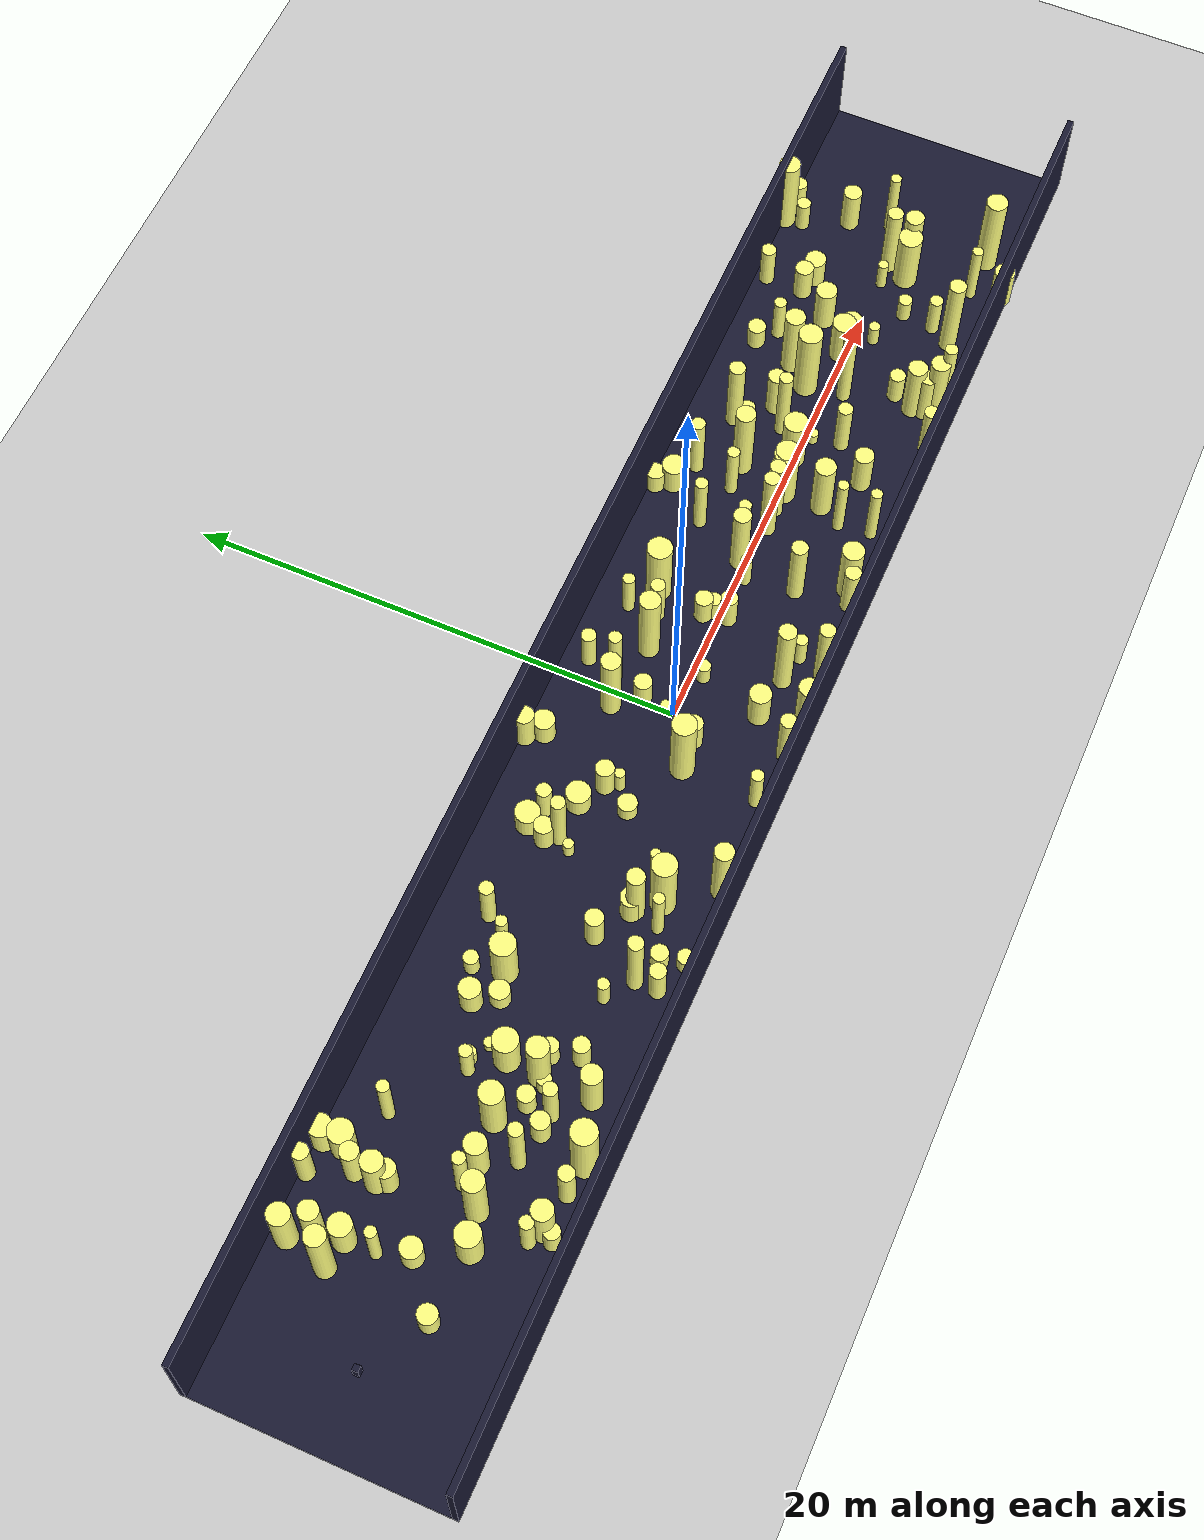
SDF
<?xml version="1.0"?>
<sdf version="1.4">
  <world name="default">
    <gui>
      <camera name="user_camera">
        <pose>-20 -30 40 0 0.66 0.83</pose>
      </camera>
    </gui>
    <include>
      <uri>model://ground_plane</uri>
    </include>
    <include>
      <uri>model://sun</uri>
    </include>
    <scene>
      <shadows>0</shadows>
    </scene>
    <model name="forest">
      <static>true</static>
      <link name="cylinder0">
        <pose>3.841317215368427 -4.510025102042122 1.7515995705522547 0 0 0 </pose>
        <visual name="visual">
          <geometry>
            <cylinder>
              <radius>0.31026531491207887</radius>
              <length>3.5031991411045094</length>
            </cylinder>
          </geometry>
          <material>
            <ambient>0.6 0.6 0.6 1</ambient>
            <diffuse>1 1 0.5 1</diffuse>
            <specular>0 0 0</specular>
            <emissive>0 0 0 1</emissive>
          </material>
        </visual>
        <collision name="collision">
          <geometry>
            <cylinder>
              <radius>0.31026531491207887</radius>
              <length>3.5031991411045094</length>
            </cylinder>
          </geometry>
          <max_contacts>0</max_contacts>
        </collision>
      </link>
      <link name="cylinder1">
        <pose>-17.237339600972607 -0.5002070811042465 1.5118524526197255 0 0 0 </pose>
        <visual name="visual">
          <geometry>
            <cylinder>
              <radius>0.46677832788261603</radius>
              <length>3.023704905239451</length>
            </cylinder>
          </geometry>
          <material>
            <ambient>0.6 0.6 0.6 1</ambient>
            <diffuse>1 1 0.5 1</diffuse>
            <specular>0 0 0</specular>
            <emissive>0 0 0 1</emissive>
          </material>
        </visual>
        <collision name="collision">
          <geometry>
            <cylinder>
              <radius>0.46677832788261603</radius>
              <length>3.023704905239451</length>
            </cylinder>
          </geometry>
          <max_contacts>0</max_contacts>
        </collision>
      </link>
      <link name="cylinder2">
        <pose>-5.597948450869204 2.804975082439764 0.8905810715772352 0 0 0 </pose>
        <visual name="visual">
          <geometry>
            <cylinder>
              <radius>0.29819938262557866</radius>
              <length>1.7811621431544704</length>
            </cylinder>
          </geometry>
          <material>
            <ambient>0.6 0.6 0.6 1</ambient>
            <diffuse>1 1 0.5 1</diffuse>
            <specular>0 0 0</specular>
            <emissive>0 0 0 1</emissive>
          </material>
        </visual>
        <collision name="collision">
          <geometry>
            <cylinder>
              <radius>0.29819938262557866</radius>
              <length>1.7811621431544704</length>
            </cylinder>
          </geometry>
          <max_contacts>0</max_contacts>
        </collision>
      </link>
      <link name="cylinder3">
        <pose>17.265367207344035 -4.435934743909113 1.9896705401178723 0 0 0 </pose>
        <visual name="visual">
          <geometry>
            <cylinder>
              <radius>0.2630179309103886</radius>
              <length>3.9793410802357445</length>
            </cylinder>
          </geometry>
          <material>
            <ambient>0.6 0.6 0.6 1</ambient>
            <diffuse>1 1 0.5 1</diffuse>
            <specular>0 0 0</specular>
            <emissive>0 0 0 1</emissive>
          </material>
        </visual>
        <collision name="collision">
          <geometry>
            <cylinder>
              <radius>0.2630179309103886</radius>
              <length>3.9793410802357445</length>
            </cylinder>
          </geometry>
          <max_contacts>0</max_contacts>
        </collision>
      </link>
      <link name="cylinder4">
        <pose>0.019550161029819435 0.3108359721676308 0.2989481723369702 0 0 0 </pose>
        <visual name="visual">
          <geometry>
            <cylinder>
              <radius>0.2081893095561564</radius>
              <length>0.5978963446739404</length>
            </cylinder>
          </geometry>
          <material>
            <ambient>0.6 0.6 0.6 1</ambient>
            <diffuse>1 1 0.5 1</diffuse>
            <specular>0 0 0</specular>
            <emissive>0 0 0 1</emissive>
          </material>
        </visual>
        <collision name="collision">
          <geometry>
            <cylinder>
              <radius>0.2081893095561564</radius>
              <length>0.5978963446739404</length>
            </cylinder>
          </geometry>
          <max_contacts>0</max_contacts>
        </collision>
      </link>
      <link name="cylinder5">
        <pose>-20.148803861511887 -3.700949633133399 1.2790488330245817 0 0 0 </pose>
        <visual name="visual">
          <geometry>
            <cylinder>
              <radius>0.4170050183967076</radius>
              <length>2.5580976660491634</length>
            </cylinder>
          </geometry>
          <material>
            <ambient>0.6 0.6 0.6 1</ambient>
            <diffuse>1 1 0.5 1</diffuse>
            <specular>0 0 0</specular>
            <emissive>0 0 0 1</emissive>
          </material>
        </visual>
        <collision name="collision">
          <geometry>
            <cylinder>
              <radius>0.4170050183967076</radius>
              <length>2.5580976660491634</length>
            </cylinder>
          </geometry>
          <max_contacts>0</max_contacts>
        </collision>
      </link>
      <link name="cylinder6">
        <pose>-8.282217289233344 -2.8858835329131693 1.393991411430147 0 0 0 </pose>
        <visual name="visual">
          <geometry>
            <cylinder>
              <radius>0.2251886929722567</radius>
              <length>2.787982822860294</length>
            </cylinder>
          </geometry>
          <material>
            <ambient>0.6 0.6 0.6 1</ambient>
            <diffuse>1 1 0.5 1</diffuse>
            <specular>0 0 0</specular>
            <emissive>0 0 0 1</emissive>
          </material>
        </visual>
        <collision name="collision">
          <geometry>
            <cylinder>
              <radius>0.2251886929722567</radius>
              <length>2.787982822860294</length>
            </cylinder>
          </geometry>
          <max_contacts>0</max_contacts>
        </collision>
      </link>
      <link name="cylinder7">
        <pose>3.7708638306672313 2.262818668443485 1.149254246026065 0 0 0 </pose>
        <visual name="visual">
          <geometry>
            <cylinder>
              <radius>0.289971947171161</radius>
              <length>2.29850849205213</length>
            </cylinder>
          </geometry>
          <material>
            <ambient>0.6 0.6 0.6 1</ambient>
            <diffuse>1 1 0.5 1</diffuse>
            <specular>0 0 0</specular>
            <emissive>0 0 0 1</emissive>
          </material>
        </visual>
        <collision name="collision">
          <geometry>
            <cylinder>
              <radius>0.289971947171161</radius>
              <length>2.29850849205213</length>
            </cylinder>
          </geometry>
          <max_contacts>0</max_contacts>
        </collision>
      </link>
      <link name="cylinder8">
        <pose>-18.899742258552887 -0.6405329994121258 1.1736366769516815 0 0 0 </pose>
        <visual name="visual">
          <geometry>
            <cylinder>
              <radius>0.4303406056270836</radius>
              <length>2.347273353903363</length>
            </cylinder>
          </geometry>
          <material>
            <ambient>0.6 0.6 0.6 1</ambient>
            <diffuse>1 1 0.5 1</diffuse>
            <specular>0 0 0</specular>
            <emissive>0 0 0 1</emissive>
          </material>
        </visual>
        <collision name="collision">
          <geometry>
            <cylinder>
              <radius>0.4303406056270836</radius>
              <length>2.347273353903363</length>
            </cylinder>
          </geometry>
          <max_contacts>0</max_contacts>
        </collision>
      </link>
      <link name="cylinder9">
        <pose>15.985617696197174 0.9436524453826465 1.8260758718976415 0 0 0 </pose>
        <visual name="visual">
          <geometry>
            <cylinder>
              <radius>0.48607248846661</radius>
              <length>3.652151743795283</length>
            </cylinder>
          </geometry>
          <material>
            <ambient>0.6 0.6 0.6 1</ambient>
            <diffuse>1 1 0.5 1</diffuse>
            <specular>0 0 0</specular>
            <emissive>0 0 0 1</emissive>
          </material>
        </visual>
        <collision name="collision">
          <geometry>
            <cylinder>
              <radius>0.48607248846661</radius>
              <length>3.652151743795283</length>
            </cylinder>
          </geometry>
          <max_contacts>0</max_contacts>
        </collision>
      </link>
      <link name="cylinder10">
        <pose>0.91863081633619 3.880131118316367 0.9672206659443383 0 0 0 </pose>
        <visual name="visual">
          <geometry>
            <cylinder>
              <radius>0.2948802282345892</radius>
              <length>1.9344413318886766</length>
            </cylinder>
          </geometry>
          <material>
            <ambient>0.6 0.6 0.6 1</ambient>
            <diffuse>1 1 0.5 1</diffuse>
            <specular>0 0 0</specular>
            <emissive>0 0 0 1</emissive>
          </material>
        </visual>
        <collision name="collision">
          <geometry>
            <cylinder>
              <radius>0.2948802282345892</radius>
              <length>1.9344413318886766</length>
            </cylinder>
          </geometry>
          <max_contacts>0</max_contacts>
        </collision>
      </link>
      <link name="cylinder11">
        <pose>-8.076823484715579 -1.7469018621044894 0.7119745542608408 0 0 0 </pose>
        <visual name="visual">
          <geometry>
            <cylinder>
              <radius>0.41168028122987677</radius>
              <length>1.4239491085216816</length>
            </cylinder>
          </geometry>
          <material>
            <ambient>0.6 0.6 0.6 1</ambient>
            <diffuse>1 1 0.5 1</diffuse>
            <specular>0 0 0</specular>
            <emissive>0 0 0 1</emissive>
          </material>
        </visual>
        <collision name="collision">
          <geometry>
            <cylinder>
              <radius>0.41168028122987677</radius>
              <length>1.4239491085216816</length>
            </cylinder>
          </geometry>
          <max_contacts>0</max_contacts>
        </collision>
      </link>
      <link name="cylinder12">
        <pose>6.380139031225884 -4.7992953907381875 0.3489111552656734 0 0 0 </pose>
        <visual name="visual">
          <geometry>
            <cylinder>
              <radius>0.28228500885628927</radius>
              <length>0.6978223105313468</length>
            </cylinder>
          </geometry>
          <material>
            <ambient>0.6 0.6 0.6 1</ambient>
            <diffuse>1 1 0.5 1</diffuse>
            <specular>0 0 0</specular>
            <emissive>0 0 0 1</emissive>
          </material>
        </visual>
        <collision name="collision">
          <geometry>
            <cylinder>
              <radius>0.28228500885628927</radius>
              <length>0.6978223105313468</length>
            </cylinder>
          </geometry>
          <max_contacts>0</max_contacts>
        </collision>
      </link>
      <link name="cylinder13">
        <pose>2.2621900080426407 1.969604160525682 1.8763601650356239 0 0 0 </pose>
        <visual name="visual">
          <geometry>
            <cylinder>
              <radius>0.4143979946371352</radius>
              <length>3.7527203300712477</length>
            </cylinder>
          </geometry>
          <material>
            <ambient>0.6 0.6 0.6 1</ambient>
            <diffuse>1 1 0.5 1</diffuse>
            <specular>0 0 0</specular>
            <emissive>0 0 0 1</emissive>
          </material>
        </visual>
        <collision name="collision">
          <geometry>
            <cylinder>
              <radius>0.4143979946371352</radius>
              <length>3.7527203300712477</length>
            </cylinder>
          </geometry>
          <max_contacts>0</max_contacts>
        </collision>
      </link>
      <link name="cylinder14">
        <pose>9.988890898511393 -0.10635863900852982 1.6012139004685157 0 0 0 </pose>
        <visual name="visual">
          <geometry>
            <cylinder>
              <radius>0.32412791843226907</radius>
              <length>3.2024278009370315</length>
            </cylinder>
          </geometry>
          <material>
            <ambient>0.6 0.6 0.6 1</ambient>
            <diffuse>1 1 0.5 1</diffuse>
            <specular>0 0 0</specular>
            <emissive>0 0 0 1</emissive>
          </material>
        </visual>
        <collision name="collision">
          <geometry>
            <cylinder>
              <radius>0.32412791843226907</radius>
              <length>3.2024278009370315</length>
            </cylinder>
          </geometry>
          <max_contacts>0</max_contacts>
        </collision>
      </link>
      <link name="cylinder15">
        <pose>-12.01330068813229 1.4757289131431541 1.3220157545991622 0 0 0 </pose>
        <visual name="visual">
          <geometry>
            <cylinder>
              <radius>0.49491867467201395</radius>
              <length>2.6440315091983244</length>
            </cylinder>
          </geometry>
          <material>
            <ambient>0.6 0.6 0.6 1</ambient>
            <diffuse>1 1 0.5 1</diffuse>
            <specular>0 0 0</specular>
            <emissive>0 0 0 1</emissive>
          </material>
        </visual>
        <collision name="collision">
          <geometry>
            <cylinder>
              <radius>0.49491867467201395</radius>
              <length>2.6440315091983244</length>
            </cylinder>
          </geometry>
          <max_contacts>0</max_contacts>
        </collision>
      </link>
      <link name="cylinder16">
        <pose>-23.48727687036992 3.24876843397006 1.731877221561158 0 0 0 </pose>
        <visual name="visual">
          <geometry>
            <cylinder>
              <radius>0.3859166150230648</radius>
              <length>3.463754443122316</length>
            </cylinder>
          </geometry>
          <material>
            <ambient>0.6 0.6 0.6 1</ambient>
            <diffuse>1 1 0.5 1</diffuse>
            <specular>0 0 0</specular>
            <emissive>0 0 0 1</emissive>
          </material>
        </visual>
        <collision name="collision">
          <geometry>
            <cylinder>
              <radius>0.3859166150230648</radius>
              <length>3.463754443122316</length>
            </cylinder>
          </geometry>
          <max_contacts>0</max_contacts>
        </collision>
      </link>
      <link name="cylinder17">
        <pose>1.929898529020484 -0.4303004359131286 0.5025351860580825 0 0 0 </pose>
        <visual name="visual">
          <geometry>
            <cylinder>
              <radius>0.2717361799213967</radius>
              <length>1.005070372116165</length>
            </cylinder>
          </geometry>
          <material>
            <ambient>0.6 0.6 0.6 1</ambient>
            <diffuse>1 1 0.5 1</diffuse>
            <specular>0 0 0</specular>
            <emissive>0 0 0 1</emissive>
          </material>
        </visual>
        <collision name="collision">
          <geometry>
            <cylinder>
              <radius>0.2717361799213967</radius>
              <length>1.005070372116165</length>
            </cylinder>
          </geometry>
          <max_contacts>0</max_contacts>
        </collision>
      </link>
      <link name="cylinder18">
        <pose>13.68541646399914 1.0580866153303345 1.800160267333065 0 0 0 </pose>
        <visual name="visual">
          <geometry>
            <cylinder>
              <radius>0.27594449265318627</radius>
              <length>3.60032053466613</length>
            </cylinder>
          </geometry>
          <material>
            <ambient>0.6 0.6 0.6 1</ambient>
            <diffuse>1 1 0.5 1</diffuse>
            <specular>0 0 0</specular>
            <emissive>0 0 0 1</emissive>
          </material>
        </visual>
        <collision name="collision">
          <geometry>
            <cylinder>
              <radius>0.27594449265318627</radius>
              <length>3.60032053466613</length>
            </cylinder>
          </geometry>
          <max_contacts>0</max_contacts>
        </collision>
      </link>
      <link name="cylinder19">
        <pose>8.306041038692413 2.3817016673894305 1.445079854383004 0 0 0 </pose>
        <visual name="visual">
          <geometry>
            <cylinder>
              <radius>0.258648438098797</radius>
              <length>2.890159708766008</length>
            </cylinder>
          </geometry>
          <material>
            <ambient>0.6 0.6 0.6 1</ambient>
            <diffuse>1 1 0.5 1</diffuse>
            <specular>0 0 0</specular>
            <emissive>0 0 0 1</emissive>
          </material>
        </visual>
        <collision name="collision">
          <geometry>
            <cylinder>
              <radius>0.258648438098797</radius>
              <length>2.890159708766008</length>
            </cylinder>
          </geometry>
          <max_contacts>0</max_contacts>
        </collision>
      </link>
      <link name="cylinder20">
        <pose>10.874119869617068 -1.7394531326744778 1.4703682676152616 0 0 0 </pose>
        <visual name="visual">
          <geometry>
            <cylinder>
              <radius>0.42072285934733505</radius>
              <length>2.9407365352305233</length>
            </cylinder>
          </geometry>
          <material>
            <ambient>0.6 0.6 0.6 1</ambient>
            <diffuse>1 1 0.5 1</diffuse>
            <specular>0 0 0</specular>
            <emissive>0 0 0 1</emissive>
          </material>
        </visual>
        <collision name="collision">
          <geometry>
            <cylinder>
              <radius>0.42072285934733505</radius>
              <length>2.9407365352305233</length>
            </cylinder>
          </geometry>
          <max_contacts>0</max_contacts>
        </collision>
      </link>
      <link name="cylinder21">
        <pose>-24.537377630705997 -1.4602951554506962 0.5840869932758881 0 0 0 </pose>
        <visual name="visual">
          <geometry>
            <cylinder>
              <radius>0.3863408214898202</radius>
              <length>1.1681739865517762</length>
            </cylinder>
          </geometry>
          <material>
            <ambient>0.6 0.6 0.6 1</ambient>
            <diffuse>1 1 0.5 1</diffuse>
            <specular>0 0 0</specular>
            <emissive>0 0 0 1</emissive>
          </material>
        </visual>
        <collision name="collision">
          <geometry>
            <cylinder>
              <radius>0.3863408214898202</radius>
              <length>1.1681739865517762</length>
            </cylinder>
          </geometry>
          <max_contacts>0</max_contacts>
        </collision>
      </link>
      <link name="cylinder22">
        <pose>-21.75738890126337 -1.6847261504267097 1.016730140741591 0 0 0 </pose>
        <visual name="visual">
          <geometry>
            <cylinder>
              <radius>0.4917726904729416</radius>
              <length>2.033460281483182</length>
            </cylinder>
          </geometry>
          <material>
            <ambient>0.6 0.6 0.6 1</ambient>
            <diffuse>1 1 0.5 1</diffuse>
            <specular>0 0 0</specular>
            <emissive>0 0 0 1</emissive>
          </material>
        </visual>
        <collision name="collision">
          <geometry>
            <cylinder>
              <radius>0.4917726904729416</radius>
              <length>2.033460281483182</length>
            </cylinder>
          </geometry>
          <max_contacts>0</max_contacts>
        </collision>
      </link>
      <link name="cylinder23">
        <pose>-15.410332753393396 -1.5987368802015167 0.46426440466343477 0 0 0 </pose>
        <visual name="visual">
          <geometry>
            <cylinder>
              <radius>0.2857012675479296</radius>
              <length>0.9285288093268695</length>
            </cylinder>
          </geometry>
          <material>
            <ambient>0.6 0.6 0.6 1</ambient>
            <diffuse>1 1 0.5 1</diffuse>
            <specular>0 0 0</specular>
            <emissive>0 0 0 1</emissive>
          </material>
        </visual>
        <collision name="collision">
          <geometry>
            <cylinder>
              <radius>0.2857012675479296</radius>
              <length>0.9285288093268695</length>
            </cylinder>
          </geometry>
          <max_contacts>0</max_contacts>
        </collision>
      </link>
      <link name="cylinder24">
        <pose>-18.463321688392135 2.998894901509825 1.4334425518272613 0 0 0 </pose>
        <visual name="visual">
          <geometry>
            <cylinder>
              <radius>0.24127743343678415</radius>
              <length>2.8668851036545226</length>
            </cylinder>
          </geometry>
          <material>
            <ambient>0.6 0.6 0.6 1</ambient>
            <diffuse>1 1 0.5 1</diffuse>
            <specular>0 0 0</specular>
            <emissive>0 0 0 1</emissive>
          </material>
        </visual>
        <collision name="collision">
          <geometry>
            <cylinder>
              <radius>0.24127743343678415</radius>
              <length>2.8668851036545226</length>
            </cylinder>
          </geometry>
          <max_contacts>0</max_contacts>
        </collision>
      </link>
      <link name="cylinder25">
        <pose>-14.300868841691312 -1.3497583953102374 0.6158416776750282 0 0 0 </pose>
        <visual name="visual">
          <geometry>
            <cylinder>
              <radius>0.32138493862074013</radius>
              <length>1.2316833553500564</length>
            </cylinder>
          </geometry>
          <material>
            <ambient>0.6 0.6 0.6 1</ambient>
            <diffuse>1 1 0.5 1</diffuse>
            <specular>0 0 0</specular>
            <emissive>0 0 0 1</emissive>
          </material>
        </visual>
        <collision name="collision">
          <geometry>
            <cylinder>
              <radius>0.32138493862074013</radius>
              <length>1.2316833553500564</length>
            </cylinder>
          </geometry>
          <max_contacts>0</max_contacts>
        </collision>
      </link>
      <link name="cylinder26">
        <pose>0.2309264891450944 1.3479970760436464 0.6541075039447826 0 0 0 </pose>
        <visual name="visual">
          <geometry>
            <cylinder>
              <radius>0.35689550213047705</radius>
              <length>1.3082150078895651</length>
            </cylinder>
          </geometry>
          <material>
            <ambient>0.6 0.6 0.6 1</ambient>
            <diffuse>1 1 0.5 1</diffuse>
            <specular>0 0 0</specular>
            <emissive>0 0 0 1</emissive>
          </material>
        </visual>
        <collision name="collision">
          <geometry>
            <cylinder>
              <radius>0.35689550213047705</radius>
              <length>1.3082150078895651</length>
            </cylinder>
          </geometry>
          <max_contacts>0</max_contacts>
        </collision>
      </link>
      <link name="cylinder27">
        <pose>-11.537661089453561 -2.1665147095185358 0.7244477340062326 0 0 0 </pose>
        <visual name="visual">
          <geometry>
            <cylinder>
              <radius>0.23354316422735868</radius>
              <length>1.4488954680124653</length>
            </cylinder>
          </geometry>
          <material>
            <ambient>0.6 0.6 0.6 1</ambient>
            <diffuse>1 1 0.5 1</diffuse>
            <specular>0 0 0</specular>
            <emissive>0 0 0 1</emissive>
          </material>
        </visual>
        <collision name="collision">
          <geometry>
            <cylinder>
              <radius>0.23354316422735868</radius>
              <length>1.4488954680124653</length>
            </cylinder>
          </geometry>
          <max_contacts>0</max_contacts>
        </collision>
      </link>
      <link name="cylinder28">
        <pose>22.040592122322238 -0.05238045770961541 0.6816336000675187 0 0 0 </pose>
        <visual name="visual">
          <geometry>
            <cylinder>
              <radius>0.2100579568130027</radius>
              <length>1.3632672001350374</length>
            </cylinder>
          </geometry>
          <material>
            <ambient>0.6 0.6 0.6 1</ambient>
            <diffuse>1 1 0.5 1</diffuse>
            <specular>0 0 0</specular>
            <emissive>0 0 0 1</emissive>
          </material>
        </visual>
        <collision name="collision">
          <geometry>
            <cylinder>
              <radius>0.2100579568130027</radius>
              <length>1.3632672001350374</length>
            </cylinder>
          </geometry>
          <max_contacts>0</max_contacts>
        </collision>
      </link>
      <link name="cylinder29">
        <pose>18.001185813643076 2.93607405292358 1.0759568169458518 0 0 0 </pose>
        <visual name="visual">
          <geometry>
            <cylinder>
              <radius>0.2527964529935181</radius>
              <length>2.1519136338917035</length>
            </cylinder>
          </geometry>
          <material>
            <ambient>0.6 0.6 0.6 1</ambient>
            <diffuse>1 1 0.5 1</diffuse>
            <specular>0 0 0</specular>
            <emissive>0 0 0 1</emissive>
          </material>
        </visual>
        <collision name="collision">
          <geometry>
            <cylinder>
              <radius>0.2527964529935181</radius>
              <length>2.1519136338917035</length>
            </cylinder>
          </geometry>
          <max_contacts>0</max_contacts>
        </collision>
      </link>
      <link name="cylinder30">
        <pose>4.462834070754685 0.6286415022368521 0.6777906479163608 0 0 0 </pose>
        <visual name="visual">
          <geometry>
            <cylinder>
              <radius>0.35982181179205497</radius>
              <length>1.3555812958327216</length>
            </cylinder>
          </geometry>
          <material>
            <ambient>0.6 0.6 0.6 1</ambient>
            <diffuse>1 1 0.5 1</diffuse>
            <specular>0 0 0</specular>
            <emissive>0 0 0 1</emissive>
          </material>
        </visual>
        <collision name="collision">
          <geometry>
            <cylinder>
              <radius>0.35982181179205497</radius>
              <length>1.3555812958327216</length>
            </cylinder>
          </geometry>
          <max_contacts>0</max_contacts>
        </collision>
      </link>
      <link name="cylinder31">
        <pose>11.01051874437303 -0.11071449453270876 1.4503504880614888 0 0 0 </pose>
        <visual name="visual">
          <geometry>
            <cylinder>
              <radius>0.4754666087721422</radius>
              <length>2.9007009761229776</length>
            </cylinder>
          </geometry>
          <material>
            <ambient>0.6 0.6 0.6 1</ambient>
            <diffuse>1 1 0.5 1</diffuse>
            <specular>0 0 0</specular>
            <emissive>0 0 0 1</emissive>
          </material>
        </visual>
        <collision name="collision">
          <geometry>
            <cylinder>
              <radius>0.4754666087721422</radius>
              <length>2.9007009761229776</length>
            </cylinder>
          </geometry>
          <max_contacts>0</max_contacts>
        </collision>
      </link>
      <link name="cylinder32">
        <pose>-3.796345316395893 1.1544314318938884 0.7949143617968951 0 0 0 </pose>
        <visual name="visual">
          <geometry>
            <cylinder>
              <radius>0.365756457904013</radius>
              <length>1.5898287235937902</length>
            </cylinder>
          </geometry>
          <material>
            <ambient>0.6 0.6 0.6 1</ambient>
            <diffuse>1 1 0.5 1</diffuse>
            <specular>0 0 0</specular>
            <emissive>0 0 0 1</emissive>
          </material>
        </visual>
        <collision name="collision">
          <geometry>
            <cylinder>
              <radius>0.365756457904013</radius>
              <length>1.5898287235937902</length>
            </cylinder>
          </geometry>
          <max_contacts>0</max_contacts>
        </collision>
      </link>
      <link name="cylinder33">
        <pose>10.72798780575858 0.021244791245167427 1.170868298967777 0 0 0 </pose>
        <visual name="visual">
          <geometry>
            <cylinder>
              <radius>0.3568445559899352</radius>
              <length>2.341736597935554</length>
            </cylinder>
          </geometry>
          <material>
            <ambient>0.6 0.6 0.6 1</ambient>
            <diffuse>1 1 0.5 1</diffuse>
            <specular>0 0 0</specular>
            <emissive>0 0 0 1</emissive>
          </material>
        </visual>
        <collision name="collision">
          <geometry>
            <cylinder>
              <radius>0.3568445559899352</radius>
              <length>2.341736597935554</length>
            </cylinder>
          </geometry>
          <max_contacts>0</max_contacts>
        </collision>
      </link>
      <link name="cylinder34">
        <pose>-2.6732552180354823 4.131881459659196 0.5983940788976321 0 0 0 </pose>
        <visual name="visual">
          <geometry>
            <cylinder>
              <radius>0.43327783691241173</radius>
              <length>1.1967881577952642</length>
            </cylinder>
          </geometry>
          <material>
            <ambient>0.6 0.6 0.6 1</ambient>
            <diffuse>1 1 0.5 1</diffuse>
            <specular>0 0 0</specular>
            <emissive>0 0 0 1</emissive>
          </material>
        </visual>
        <collision name="collision">
          <geometry>
            <cylinder>
              <radius>0.43327783691241173</radius>
              <length>1.1967881577952642</length>
            </cylinder>
          </geometry>
          <max_contacts>0</max_contacts>
        </collision>
      </link>
      <link name="cylinder35">
        <pose>16.19008777836767 -0.6306350934050116 1.9619961511160935 0 0 0 </pose>
        <visual name="visual">
          <geometry>
            <cylinder>
              <radius>0.27798618074931264</radius>
              <length>3.923992302232187</length>
            </cylinder>
          </geometry>
          <material>
            <ambient>0.6 0.6 0.6 1</ambient>
            <diffuse>1 1 0.5 1</diffuse>
            <specular>0 0 0</specular>
            <emissive>0 0 0 1</emissive>
          </material>
        </visual>
        <collision name="collision">
          <geometry>
            <cylinder>
              <radius>0.27798618074931264</radius>
              <length>3.923992302232187</length>
            </cylinder>
          </geometry>
          <max_contacts>0</max_contacts>
        </collision>
      </link>
      <link name="cylinder36">
        <pose>-6.35559475268046 3.1368418222198677 0.5620536814726268 0 0 0 </pose>
        <visual name="visual">
          <geometry>
            <cylinder>
              <radius>0.48547790595488055</radius>
              <length>1.1241073629452536</length>
            </cylinder>
          </geometry>
          <material>
            <ambient>0.6 0.6 0.6 1</ambient>
            <diffuse>1 1 0.5 1</diffuse>
            <specular>0 0 0</specular>
            <emissive>0 0 0 1</emissive>
          </material>
        </visual>
        <collision name="collision">
          <geometry>
            <cylinder>
              <radius>0.48547790595488055</radius>
              <length>1.1241073629452536</length>
            </cylinder>
          </geometry>
          <max_contacts>0</max_contacts>
        </collision>
      </link>
      <link name="cylinder37">
        <pose>-3.095924319595884 4.737810121953949 0.9232503737884867 0 0 0 </pose>
        <visual name="visual">
          <geometry>
            <cylinder>
              <radius>0.39096043442895345</radius>
              <length>1.8465007475769735</length>
            </cylinder>
          </geometry>
          <material>
            <ambient>0.6 0.6 0.6 1</ambient>
            <diffuse>1 1 0.5 1</diffuse>
            <specular>0 0 0</specular>
            <emissive>0 0 0 1</emissive>
          </material>
        </visual>
        <collision name="collision">
          <geometry>
            <cylinder>
              <radius>0.39096043442895345</radius>
              <length>1.8465007475769735</length>
            </cylinder>
          </geometry>
          <max_contacts>0</max_contacts>
        </collision>
      </link>
      <link name="cylinder38">
        <pose>-11.38642349813843 1.8052967436921499 1.5200985591942313 0 0 0 </pose>
        <visual name="visual">
          <geometry>
            <cylinder>
              <radius>0.22462556854759153</radius>
              <length>3.0401971183884626</length>
            </cylinder>
          </geometry>
          <material>
            <ambient>0.6 0.6 0.6 1</ambient>
            <diffuse>1 1 0.5 1</diffuse>
            <specular>0 0 0</specular>
            <emissive>0 0 0 1</emissive>
          </material>
        </visual>
        <collision name="collision">
          <geometry>
            <cylinder>
              <radius>0.22462556854759153</radius>
              <length>3.0401971183884626</length>
            </cylinder>
          </geometry>
          <max_contacts>0</max_contacts>
        </collision>
      </link>
      <link name="cylinder39">
        <pose>7.102698243742864 -4.34941484922842 1.265890437416562 0 0 0 </pose>
        <visual name="visual">
          <geometry>
            <cylinder>
              <radius>0.3223717352639373</radius>
              <length>2.531780874833124</length>
            </cylinder>
          </geometry>
          <material>
            <ambient>0.6 0.6 0.6 1</ambient>
            <diffuse>1 1 0.5 1</diffuse>
            <specular>0 0 0</specular>
            <emissive>0 0 0 1</emissive>
          </material>
        </visual>
        <collision name="collision">
          <geometry>
            <cylinder>
              <radius>0.3223717352639373</radius>
              <length>2.531780874833124</length>
            </cylinder>
          </geometry>
          <max_contacts>0</max_contacts>
        </collision>
      </link>
      <link name="cylinder40">
        <pose>10.660524633554068 3.499946105512384 1.5432281684198523 0 0 0 </pose>
        <visual name="visual">
          <geometry>
            <cylinder>
              <radius>0.28470364802899606</radius>
              <length>3.0864563368397047</length>
            </cylinder>
          </geometry>
          <material>
            <ambient>0.6 0.6 0.6 1</ambient>
            <diffuse>1 1 0.5 1</diffuse>
            <specular>0 0 0</specular>
            <emissive>0 0 0 1</emissive>
          </material>
        </visual>
        <collision name="collision">
          <geometry>
            <cylinder>
              <radius>0.28470364802899606</radius>
              <length>3.0864563368397047</length>
            </cylinder>
          </geometry>
          <max_contacts>0</max_contacts>
        </collision>
      </link>
      <link name="cylinder41">
        <pose>12.53007402628738 -2.78212828602196 1.0298456456420904 0 0 0 </pose>
        <visual name="visual">
          <geometry>
            <cylinder>
              <radius>0.3911711873929431</radius>
              <length>2.0596912912841807</length>
            </cylinder>
          </geometry>
          <material>
            <ambient>0.6 0.6 0.6 1</ambient>
            <diffuse>1 1 0.5 1</diffuse>
            <specular>0 0 0</specular>
            <emissive>0 0 0 1</emissive>
          </material>
        </visual>
        <collision name="collision">
          <geometry>
            <cylinder>
              <radius>0.3911711873929431</radius>
              <length>2.0596912912841807</length>
            </cylinder>
          </geometry>
          <max_contacts>0</max_contacts>
        </collision>
      </link>
      <link name="cylinder42">
        <pose>10.472146141614168 -3.9869977058093253 1.498618579816737 0 0 0 </pose>
        <visual name="visual">
          <geometry>
            <cylinder>
              <radius>0.2275832722975526</radius>
              <length>2.997237159633474</length>
            </cylinder>
          </geometry>
          <material>
            <ambient>0.6 0.6 0.6 1</ambient>
            <diffuse>1 1 0.5 1</diffuse>
            <specular>0 0 0</specular>
            <emissive>0 0 0 1</emissive>
          </material>
        </visual>
        <collision name="collision">
          <geometry>
            <cylinder>
              <radius>0.2275832722975526</radius>
              <length>2.997237159633474</length>
            </cylinder>
          </geometry>
          <max_contacts>0</max_contacts>
        </collision>
      </link>
      <link name="cylinder43">
        <pose>10.32296397878433 -2.6706954009681927 1.505286474879933 0 0 0 </pose>
        <visual name="visual">
          <geometry>
            <cylinder>
              <radius>0.22288538479372974</radius>
              <length>3.010572949759866</length>
            </cylinder>
          </geometry>
          <material>
            <ambient>0.6 0.6 0.6 1</ambient>
            <diffuse>1 1 0.5 1</diffuse>
            <specular>0 0 0</specular>
            <emissive>0 0 0 1</emissive>
          </material>
        </visual>
        <collision name="collision">
          <geometry>
            <cylinder>
              <radius>0.22288538479372974</radius>
              <length>3.010572949759866</length>
            </cylinder>
          </geometry>
          <max_contacts>0</max_contacts>
        </collision>
      </link>
      <link name="cylinder44">
        <pose>0.3830671801895775 2.5625183491541783 1.799898482044093 0 0 0 </pose>
        <visual name="visual">
          <geometry>
            <cylinder>
              <radius>0.25923744063709525</radius>
              <length>3.599796964088186</length>
            </cylinder>
          </geometry>
          <material>
            <ambient>0.6 0.6 0.6 1</ambient>
            <diffuse>1 1 0.5 1</diffuse>
            <specular>0 0 0</specular>
            <emissive>0 0 0 1</emissive>
          </material>
        </visual>
        <collision name="collision">
          <geometry>
            <cylinder>
              <radius>0.25923744063709525</radius>
              <length>3.599796964088186</length>
            </cylinder>
          </geometry>
          <max_contacts>0</max_contacts>
        </collision>
      </link>
      <link name="cylinder45">
        <pose>-17.436922142166374 -4.038939459190089 1.8130169733389931 0 0 0 </pose>
        <visual name="visual">
          <geometry>
            <cylinder>
              <radius>0.498983910959908</radius>
              <length>3.6260339466779863</length>
            </cylinder>
          </geometry>
          <material>
            <ambient>0.6 0.6 0.6 1</ambient>
            <diffuse>1 1 0.5 1</diffuse>
            <specular>0 0 0</specular>
            <emissive>0 0 0 1</emissive>
          </material>
        </visual>
        <collision name="collision">
          <geometry>
            <cylinder>
              <radius>0.498983910959908</radius>
              <length>3.6260339466779863</length>
            </cylinder>
          </geometry>
          <max_contacts>0</max_contacts>
        </collision>
      </link>
      <link name="cylinder46">
        <pose>22.66913237175904 -0.8634470856299306 1.4013999313948315 0 0 0 </pose>
        <visual name="visual">
          <geometry>
            <cylinder>
              <radius>0.4897266639417963</radius>
              <length>2.802799862789663</length>
            </cylinder>
          </geometry>
          <material>
            <ambient>0.6 0.6 0.6 1</ambient>
            <diffuse>1 1 0.5 1</diffuse>
            <specular>0 0 0</specular>
            <emissive>0 0 0 1</emissive>
          </material>
        </visual>
        <collision name="collision">
          <geometry>
            <cylinder>
              <radius>0.4897266639417963</radius>
              <length>2.802799862789663</length>
            </cylinder>
          </geometry>
          <max_contacts>0</max_contacts>
        </collision>
      </link>
      <link name="cylinder47">
        <pose>-9.488001945957015 -0.9172338314719717 0.9083555281805161 0 0 0 </pose>
        <visual name="visual">
          <geometry>
            <cylinder>
              <radius>0.3570390345416714</radius>
              <length>1.8167110563610323</length>
            </cylinder>
          </geometry>
          <material>
            <ambient>0.6 0.6 0.6 1</ambient>
            <diffuse>1 1 0.5 1</diffuse>
            <specular>0 0 0</specular>
            <emissive>0 0 0 1</emissive>
          </material>
        </visual>
        <collision name="collision">
          <geometry>
            <cylinder>
              <radius>0.3570390345416714</radius>
              <length>1.8167110563610323</length>
            </cylinder>
          </geometry>
          <max_contacts>0</max_contacts>
        </collision>
      </link>
      <link name="cylinder48">
        <pose>-9.19745577396438 -4.3574099252883824 0.4262601787624855 0 0 0 </pose>
        <visual name="visual">
          <geometry>
            <cylinder>
              <radius>0.3205312203798536</radius>
              <length>0.852520357524971</length>
            </cylinder>
          </geometry>
          <material>
            <ambient>0.6 0.6 0.6 1</ambient>
            <diffuse>1 1 0.5 1</diffuse>
            <specular>0 0 0</specular>
            <emissive>0 0 0 1</emissive>
          </material>
        </visual>
        <collision name="collision">
          <geometry>
            <cylinder>
              <radius>0.3205312203798536</radius>
              <length>0.852520357524971</length>
            </cylinder>
          </geometry>
          <max_contacts>0</max_contacts>
        </collision>
      </link>
      <link name="cylinder49">
        <pose>14.550531728049812 1.71483162596736 1.1135379873972044 0 0 0 </pose>
        <visual name="visual">
          <geometry>
            <cylinder>
              <radius>0.3496545029271595</radius>
              <length>2.227075974794409</length>
            </cylinder>
          </geometry>
          <material>
            <ambient>0.6 0.6 0.6 1</ambient>
            <diffuse>1 1 0.5 1</diffuse>
            <specular>0 0 0</specular>
            <emissive>0 0 0 1</emissive>
          </material>
        </visual>
        <collision name="collision">
          <geometry>
            <cylinder>
              <radius>0.3496545029271595</radius>
              <length>2.227075974794409</length>
            </cylinder>
          </geometry>
          <max_contacts>0</max_contacts>
        </collision>
      </link>
      <link name="cylinder50">
        <pose>-20.8830408254851 2.283387764054501 1.2281981433649296 0 0 0 </pose>
        <visual name="visual">
          <geometry>
            <cylinder>
              <radius>0.42596792324083055</radius>
              <length>2.456396286729859</length>
            </cylinder>
          </geometry>
          <material>
            <ambient>0.6 0.6 0.6 1</ambient>
            <diffuse>1 1 0.5 1</diffuse>
            <specular>0 0 0</specular>
            <emissive>0 0 0 1</emissive>
          </material>
        </visual>
        <collision name="collision">
          <geometry>
            <cylinder>
              <radius>0.42596792324083055</radius>
              <length>2.456396286729859</length>
            </cylinder>
          </geometry>
          <max_contacts>0</max_contacts>
        </collision>
      </link>
      <link name="cylinder51">
        <pose>-6.780115979278612 1.3118215421467063 0.3928608949409351 0 0 0 </pose>
        <visual name="visual">
          <geometry>
            <cylinder>
              <radius>0.21145059637063282</radius>
              <length>0.7857217898818702</length>
            </cylinder>
          </geometry>
          <material>
            <ambient>0.6 0.6 0.6 1</ambient>
            <diffuse>1 1 0.5 1</diffuse>
            <specular>0 0 0</specular>
            <emissive>0 0 0 1</emissive>
          </material>
        </visual>
        <collision name="collision">
          <geometry>
            <cylinder>
              <radius>0.21145059637063282</radius>
              <length>0.7857217898818702</length>
            </cylinder>
          </geometry>
          <max_contacts>0</max_contacts>
        </collision>
      </link>
      <link name="cylinder52">
        <pose>10.234479679962988 1.834083787359745 1.3494731141163883 0 0 0 </pose>
        <visual name="visual">
          <geometry>
            <cylinder>
              <radius>0.2448913619247631</radius>
              <length>2.6989462282327765</length>
            </cylinder>
          </geometry>
          <material>
            <ambient>0.6 0.6 0.6 1</ambient>
            <diffuse>1 1 0.5 1</diffuse>
            <specular>0 0 0</specular>
            <emissive>0 0 0 1</emissive>
          </material>
        </visual>
        <collision name="collision">
          <geometry>
            <cylinder>
              <radius>0.2448913619247631</radius>
              <length>2.6989462282327765</length>
            </cylinder>
          </geometry>
          <max_contacts>0</max_contacts>
        </collision>
      </link>
      <link name="cylinder53">
        <pose>23.356790306379672 -4.807205801807449 0.8871020642010183 0 0 0 </pose>
        <visual name="visual">
          <geometry>
            <cylinder>
              <radius>0.422632846903202</radius>
              <length>1.7742041284020367</length>
            </cylinder>
          </geometry>
          <material>
            <ambient>0.6 0.6 0.6 1</ambient>
            <diffuse>1 1 0.5 1</diffuse>
            <specular>0 0 0</specular>
            <emissive>0 0 0 1</emissive>
          </material>
        </visual>
        <collision name="collision">
          <geometry>
            <cylinder>
              <radius>0.422632846903202</radius>
              <length>1.7742041284020367</length>
            </cylinder>
          </geometry>
          <max_contacts>0</max_contacts>
        </collision>
      </link>
      <link name="cylinder54">
        <pose>24.487264170975486 2.290624101335781 1.0378243851109623 0 0 0 </pose>
        <visual name="visual">
          <geometry>
            <cylinder>
              <radius>0.3793264267058001</radius>
              <length>2.0756487702219246</length>
            </cylinder>
          </geometry>
          <material>
            <ambient>0.6 0.6 0.6 1</ambient>
            <diffuse>1 1 0.5 1</diffuse>
            <specular>0 0 0</specular>
            <emissive>0 0 0 1</emissive>
          </material>
        </visual>
        <collision name="collision">
          <geometry>
            <cylinder>
              <radius>0.3793264267058001</radius>
              <length>2.0756487702219246</length>
            </cylinder>
          </geometry>
          <max_contacts>0</max_contacts>
        </collision>
      </link>
      <link name="cylinder55">
        <pose>7.7459871634726625 -4.074351131952453 1.4843948495885289 0 0 0 </pose>
        <visual name="visual">
          <geometry>
            <cylinder>
              <radius>0.43689139145279654</radius>
              <length>2.9687896991770577</length>
            </cylinder>
          </geometry>
          <material>
            <ambient>0.6 0.6 0.6 1</ambient>
            <diffuse>1 1 0.5 1</diffuse>
            <specular>0 0 0</specular>
            <emissive>0 0 0 1</emissive>
          </material>
        </visual>
        <collision name="collision">
          <geometry>
            <cylinder>
              <radius>0.43689139145279654</radius>
              <length>2.9687896991770577</length>
            </cylinder>
          </geometry>
          <max_contacts>0</max_contacts>
        </collision>
      </link>
      <link name="cylinder56">
        <pose>23.627475249869676 4.087026613910105 0.7262262632417797 0 0 0 </pose>
        <visual name="visual">
          <geometry>
            <cylinder>
              <radius>0.28653496977783505</radius>
              <length>1.4524525264835595</length>
            </cylinder>
          </geometry>
          <material>
            <ambient>0.6 0.6 0.6 1</ambient>
            <diffuse>1 1 0.5 1</diffuse>
            <specular>0 0 0</specular>
            <emissive>0 0 0 1</emissive>
          </material>
        </visual>
        <collision name="collision">
          <geometry>
            <cylinder>
              <radius>0.28653496977783505</radius>
              <length>1.4524525264835595</length>
            </cylinder>
          </geometry>
          <max_contacts>0</max_contacts>
        </collision>
      </link>
      <link name="cylinder57">
        <pose>-15.513438105112614 1.2278613242603136 0.40785494889892826 0 0 0 </pose>
        <visual name="visual">
          <geometry>
            <cylinder>
              <radius>0.25544507673638867</radius>
              <length>0.8157098977978565</length>
            </cylinder>
          </geometry>
          <material>
            <ambient>0.6 0.6 0.6 1</ambient>
            <diffuse>1 1 0.5 1</diffuse>
            <specular>0 0 0</specular>
            <emissive>0 0 0 1</emissive>
          </material>
        </visual>
        <collision name="collision">
          <geometry>
            <cylinder>
              <radius>0.25544507673638867</radius>
              <length>0.8157098977978565</length>
            </cylinder>
          </geometry>
          <max_contacts>0</max_contacts>
        </collision>
      </link>
      <link name="cylinder58">
        <pose>-14.810555365355022 0.7895955618574657 0.24189875727437865 0 0 0 </pose>
        <visual name="visual">
          <geometry>
            <cylinder>
              <radius>0.20906370584355957</radius>
              <length>0.4837975145487573</length>
            </cylinder>
          </geometry>
          <material>
            <ambient>0.6 0.6 0.6 1</ambient>
            <diffuse>1 1 0.5 1</diffuse>
            <specular>0 0 0</specular>
            <emissive>0 0 0 1</emissive>
          </material>
        </visual>
        <collision name="collision">
          <geometry>
            <cylinder>
              <radius>0.20906370584355957</radius>
              <length>0.4837975145487573</length>
            </cylinder>
          </geometry>
          <max_contacts>0</max_contacts>
        </collision>
      </link>
      <link name="cylinder59">
        <pose>-24.262080580485474 2.5780756254650044 1.9414825914702964 0 0 0 </pose>
        <visual name="visual">
          <geometry>
            <cylinder>
              <radius>0.4035563122428887</radius>
              <length>3.882965182940593</length>
            </cylinder>
          </geometry>
          <material>
            <ambient>0.6 0.6 0.6 1</ambient>
            <diffuse>1 1 0.5 1</diffuse>
            <specular>0 0 0</specular>
            <emissive>0 0 0 1</emissive>
          </material>
        </visual>
        <collision name="collision">
          <geometry>
            <cylinder>
              <radius>0.4035563122428887</radius>
              <length>3.882965182940593</length>
            </cylinder>
          </geometry>
          <max_contacts>0</max_contacts>
        </collision>
      </link>
      <link name="cylinder60">
        <pose>23.03389517982226 -3.6052778285962206 1.4446867309733429 0 0 0 </pose>
        <visual name="visual">
          <geometry>
            <cylinder>
              <radius>0.22329579768393998</radius>
              <length>2.8893734619466858</length>
            </cylinder>
          </geometry>
          <material>
            <ambient>0.6 0.6 0.6 1</ambient>
            <diffuse>1 1 0.5 1</diffuse>
            <specular>0 0 0</specular>
            <emissive>0 0 0 1</emissive>
          </material>
        </visual>
        <collision name="collision">
          <geometry>
            <cylinder>
              <radius>0.22329579768393998</radius>
              <length>2.8893734619466858</length>
            </cylinder>
          </geometry>
          <max_contacts>0</max_contacts>
        </collision>
      </link>
      <link name="cylinder61">
        <pose>20.3746311714783 2.7949430357938176 0.8248853213016196 0 0 0 </pose>
        <visual name="visual">
          <geometry>
            <cylinder>
              <radius>0.37489593620173245</radius>
              <length>1.6497706426032392</length>
            </cylinder>
          </geometry>
          <material>
            <ambient>0.6 0.6 0.6 1</ambient>
            <diffuse>1 1 0.5 1</diffuse>
            <specular>0 0 0</specular>
            <emissive>0 0 0 1</emissive>
          </material>
        </visual>
        <collision name="collision">
          <geometry>
            <cylinder>
              <radius>0.37489593620173245</radius>
              <length>1.6497706426032392</length>
            </cylinder>
          </geometry>
          <max_contacts>0</max_contacts>
        </collision>
      </link>
      <link name="cylinder62">
        <pose>-20.72868564199508 1.9059651147502112 0.8606134711768242 0 0 0 </pose>
        <visual name="visual">
          <geometry>
            <cylinder>
              <radius>0.3852916599648989</radius>
              <length>1.7212269423536484</length>
            </cylinder>
          </geometry>
          <material>
            <ambient>0.6 0.6 0.6 1</ambient>
            <diffuse>1 1 0.5 1</diffuse>
            <specular>0 0 0</specular>
            <emissive>0 0 0 1</emissive>
          </material>
        </visual>
        <collision name="collision">
          <geometry>
            <cylinder>
              <radius>0.3852916599648989</radius>
              <length>1.7212269423536484</length>
            </cylinder>
          </geometry>
          <max_contacts>0</max_contacts>
        </collision>
      </link>
      <link name="cylinder63">
        <pose>-15.022772718436128 0.02190572271629243 1.035968711681472 0 0 0 </pose>
        <visual name="visual">
          <geometry>
            <cylinder>
              <radius>0.4952670084634616</radius>
              <length>2.071937423362944</length>
            </cylinder>
          </geometry>
          <material>
            <ambient>0.6 0.6 0.6 1</ambient>
            <diffuse>1 1 0.5 1</diffuse>
            <specular>0 0 0</specular>
            <emissive>0 0 0 1</emissive>
          </material>
        </visual>
        <collision name="collision">
          <geometry>
            <cylinder>
              <radius>0.4952670084634616</radius>
              <length>2.071937423362944</length>
            </cylinder>
          </geometry>
          <max_contacts>0</max_contacts>
        </collision>
      </link>
      <link name="cylinder64">
        <pose>-13.54979081818583 2.1038303310756623 0.6987976968159539 0 0 0 </pose>
        <visual name="visual">
          <geometry>
            <cylinder>
              <radius>0.42614444110148797</radius>
              <length>1.3975953936319079</length>
            </cylinder>
          </geometry>
          <material>
            <ambient>0.6 0.6 0.6 1</ambient>
            <diffuse>1 1 0.5 1</diffuse>
            <specular>0 0 0</specular>
            <emissive>0 0 0 1</emissive>
          </material>
        </visual>
        <collision name="collision">
          <geometry>
            <cylinder>
              <radius>0.42614444110148797</radius>
              <length>1.3975953936319079</length>
            </cylinder>
          </geometry>
          <max_contacts>0</max_contacts>
        </collision>
      </link>
      <link name="cylinder65">
        <pose>24.938961947113484 0.6699475104403003 1.618653470126563 0 0 0 </pose>
        <visual name="visual">
          <geometry>
            <cylinder>
              <radius>0.2213672401464681</radius>
              <length>3.237306940253126</length>
            </cylinder>
          </geometry>
          <material>
            <ambient>0.6 0.6 0.6 1</ambient>
            <diffuse>1 1 0.5 1</diffuse>
            <specular>0 0 0</specular>
            <emissive>0 0 0 1</emissive>
          </material>
        </visual>
        <collision name="collision">
          <geometry>
            <cylinder>
              <radius>0.2213672401464681</radius>
              <length>3.237306940253126</length>
            </cylinder>
          </geometry>
          <max_contacts>0</max_contacts>
        </collision>
      </link>
      <link name="cylinder66">
        <pose>13.68109060385482 -0.28891109133629733 0.28853526098540355 0 0 0 </pose>
        <visual name="visual">
          <geometry>
            <cylinder>
              <radius>0.20655135310104455</radius>
              <length>0.5770705219708071</length>
            </cylinder>
          </geometry>
          <material>
            <ambient>0.6 0.6 0.6 1</ambient>
            <diffuse>1 1 0.5 1</diffuse>
            <specular>0 0 0</specular>
            <emissive>0 0 0 1</emissive>
          </material>
        </visual>
        <collision name="collision">
          <geometry>
            <cylinder>
              <radius>0.20655135310104455</radius>
              <length>0.5770705219708071</length>
            </cylinder>
          </geometry>
          <max_contacts>0</max_contacts>
        </collision>
      </link>
      <link name="cylinder67">
        <pose>-20.42855529650008 -1.3215768000717576 1.7597092344462273 0 0 0 </pose>
        <visual name="visual">
          <geometry>
            <cylinder>
              <radius>0.42798806121495264</radius>
              <length>3.5194184688924546</length>
            </cylinder>
          </geometry>
          <material>
            <ambient>0.6 0.6 0.6 1</ambient>
            <diffuse>1 1 0.5 1</diffuse>
            <specular>0 0 0</specular>
            <emissive>0 0 0 1</emissive>
          </material>
        </visual>
        <collision name="collision">
          <geometry>
            <cylinder>
              <radius>0.42798806121495264</radius>
              <length>3.5194184688924546</length>
            </cylinder>
          </geometry>
          <max_contacts>0</max_contacts>
        </collision>
      </link>
      <link name="cylinder68">
        <pose>15.114163099118024 -4.56909536329378 1.3134578329043127 0 0 0 </pose>
        <visual name="visual">
          <geometry>
            <cylinder>
              <radius>0.3001657237598002</radius>
              <length>2.6269156658086255</length>
            </cylinder>
          </geometry>
          <material>
            <ambient>0.6 0.6 0.6 1</ambient>
            <diffuse>1 1 0.5 1</diffuse>
            <specular>0 0 0</specular>
            <emissive>0 0 0 1</emissive>
          </material>
        </visual>
        <collision name="collision">
          <geometry>
            <cylinder>
              <radius>0.3001657237598002</radius>
              <length>2.6269156658086255</length>
            </cylinder>
          </geometry>
          <max_contacts>0</max_contacts>
        </collision>
      </link>
      <link name="cylinder69">
        <pose>-18.26102557763499 -1.8956662297669413 1.7904086044783356 0 0 0 </pose>
        <visual name="visual">
          <geometry>
            <cylinder>
              <radius>0.2803412955227197</radius>
              <length>3.580817208956671</length>
            </cylinder>
          </geometry>
          <material>
            <ambient>0.6 0.6 0.6 1</ambient>
            <diffuse>1 1 0.5 1</diffuse>
            <specular>0 0 0</specular>
            <emissive>0 0 0 1</emissive>
          </material>
        </visual>
        <collision name="collision">
          <geometry>
            <cylinder>
              <radius>0.2803412955227197</radius>
              <length>3.580817208956671</length>
            </cylinder>
          </geometry>
          <max_contacts>0</max_contacts>
        </collision>
      </link>
      <link name="cylinder70">
        <pose>19.263962168119868 0.19779896826057097 0.4688701589837203 0 0 0 </pose>
        <visual name="visual">
          <geometry>
            <cylinder>
              <radius>0.3955365020443804</radius>
              <length>0.9377403179674406</length>
            </cylinder>
          </geometry>
          <material>
            <ambient>0.6 0.6 0.6 1</ambient>
            <diffuse>1 1 0.5 1</diffuse>
            <specular>0 0 0</specular>
            <emissive>0 0 0 1</emissive>
          </material>
        </visual>
        <collision name="collision">
          <geometry>
            <cylinder>
              <radius>0.3955365020443804</radius>
              <length>0.9377403179674406</length>
            </cylinder>
          </geometry>
          <max_contacts>0</max_contacts>
        </collision>
      </link>
      <link name="cylinder71">
        <pose>0.08797585774895111 -4.488098372799972 1.421899643626729 0 0 0 </pose>
        <visual name="visual">
          <geometry>
            <cylinder>
              <radius>0.3147950107686442</radius>
              <length>2.843799287253458</length>
            </cylinder>
          </geometry>
          <material>
            <ambient>0.6 0.6 0.6 1</ambient>
            <diffuse>1 1 0.5 1</diffuse>
            <specular>0 0 0</specular>
            <emissive>0 0 0 1</emissive>
          </material>
        </visual>
        <collision name="collision">
          <geometry>
            <cylinder>
              <radius>0.3147950107686442</radius>
              <length>2.843799287253458</length>
            </cylinder>
          </geometry>
          <max_contacts>0</max_contacts>
        </collision>
      </link>
      <link name="cylinder72">
        <pose>18.10067956637038 0.20889789100631262 1.0684822231156716 0 0 0 </pose>
        <visual name="visual">
          <geometry>
            <cylinder>
              <radius>0.4791515794332464</radius>
              <length>2.1369644462313433</length>
            </cylinder>
          </geometry>
          <material>
            <ambient>0.6 0.6 0.6 1</ambient>
            <diffuse>1 1 0.5 1</diffuse>
            <specular>0 0 0</specular>
            <emissive>0 0 0 1</emissive>
          </material>
        </visual>
        <collision name="collision">
          <geometry>
            <cylinder>
              <radius>0.4791515794332464</radius>
              <length>2.1369644462313433</length>
            </cylinder>
          </geometry>
          <max_contacts>0</max_contacts>
        </collision>
      </link>
      <link name="cylinder73">
        <pose>9.32625209024728 0.8686492263503265 0.3891782524136886 0 0 0 </pose>
        <visual name="visual">
          <geometry>
            <cylinder>
              <radius>0.2536598950467473</radius>
              <length>0.7783565048273772</length>
            </cylinder>
          </geometry>
          <material>
            <ambient>0.6 0.6 0.6 1</ambient>
            <diffuse>1 1 0.5 1</diffuse>
            <specular>0 0 0</specular>
            <emissive>0 0 0 1</emissive>
          </material>
        </visual>
        <collision name="collision">
          <geometry>
            <cylinder>
              <radius>0.2536598950467473</radius>
              <length>0.7783565048273772</length>
            </cylinder>
          </geometry>
          <max_contacts>0</max_contacts>
        </collision>
      </link>
      <link name="cylinder74">
        <pose>-20.702714968685665 -3.374078118057521 1.2034732354549333 0 0 0 </pose>
        <visual name="visual">
          <geometry>
            <cylinder>
              <radius>0.2649725305576209</radius>
              <length>2.4069464709098667</length>
            </cylinder>
          </geometry>
          <material>
            <ambient>0.6 0.6 0.6 1</ambient>
            <diffuse>1 1 0.5 1</diffuse>
            <specular>0 0 0</specular>
            <emissive>0 0 0 1</emissive>
          </material>
        </visual>
        <collision name="collision">
          <geometry>
            <cylinder>
              <radius>0.2649725305576209</radius>
              <length>2.4069464709098667</length>
            </cylinder>
          </geometry>
          <max_contacts>0</max_contacts>
        </collision>
      </link>
      <link name="cylinder75">
        <pose>24.48148417213259 4.6067890700501 0.7538468771736562 0 0 0 </pose>
        <visual name="visual">
          <geometry>
            <cylinder>
              <radius>0.30800400913168346</radius>
              <length>1.5076937543473123</length>
            </cylinder>
          </geometry>
          <material>
            <ambient>0.6 0.6 0.6 1</ambient>
            <diffuse>1 1 0.5 1</diffuse>
            <specular>0 0 0</specular>
            <emissive>0 0 0 1</emissive>
          </material>
        </visual>
        <collision name="collision">
          <geometry>
            <cylinder>
              <radius>0.30800400913168346</radius>
              <length>1.5076937543473123</length>
            </cylinder>
          </geometry>
          <max_contacts>0</max_contacts>
        </collision>
      </link>
      <link name="cylinder76">
        <pose>-6.701389511142825 2.3363827033485443 0.6730518160234639 0 0 0 </pose>
        <visual name="visual">
          <geometry>
            <cylinder>
              <radius>0.3760755214761362</radius>
              <length>1.3461036320469277</length>
            </cylinder>
          </geometry>
          <material>
            <ambient>0.6 0.6 0.6 1</ambient>
            <diffuse>1 1 0.5 1</diffuse>
            <specular>0 0 0</specular>
            <emissive>0 0 0 1</emissive>
          </material>
        </visual>
        <collision name="collision">
          <geometry>
            <cylinder>
              <radius>0.3760755214761362</radius>
              <length>1.3461036320469277</length>
            </cylinder>
          </geometry>
          <max_contacts>0</max_contacts>
        </collision>
      </link>
      <link name="cylinder77">
        <pose>20.762198931305193 -2.7679373218280547 0.9660033638375523 0 0 0 </pose>
        <visual name="visual">
          <geometry>
            <cylinder>
              <radius>0.2704505073360964</radius>
              <length>1.9320067276751045</length>
            </cylinder>
          </geometry>
          <material>
            <ambient>0.6 0.6 0.6 1</ambient>
            <diffuse>1 1 0.5 1</diffuse>
            <specular>0 0 0</specular>
            <emissive>0 0 0 1</emissive>
          </material>
        </visual>
        <collision name="collision">
          <geometry>
            <cylinder>
              <radius>0.2704505073360964</radius>
              <length>1.9320067276751045</length>
            </cylinder>
          </geometry>
          <max_contacts>0</max_contacts>
        </collision>
      </link>
      <link name="cylinder78">
        <pose>19.21857678669612 -0.7650855328971566 0.5173898636561053 0 0 0 </pose>
        <visual name="visual">
          <geometry>
            <cylinder>
              <radius>0.2279455137779284</radius>
              <length>1.0347797273122106</length>
            </cylinder>
          </geometry>
          <material>
            <ambient>0.6 0.6 0.6 1</ambient>
            <diffuse>1 1 0.5 1</diffuse>
            <specular>0 0 0</specular>
            <emissive>0 0 0 1</emissive>
          </material>
        </visual>
        <collision name="collision">
          <geometry>
            <cylinder>
              <radius>0.2279455137779284</radius>
              <length>1.0347797273122106</length>
            </cylinder>
          </geometry>
          <max_contacts>0</max_contacts>
        </collision>
      </link>
      <link name="cylinder79">
        <pose>-13.024787491578005 1.2041272170164259 0.4677098413487476 0 0 0 </pose>
        <visual name="visual">
          <geometry>
            <cylinder>
              <radius>0.4015944960963625</radius>
              <length>0.9354196826974952</length>
            </cylinder>
          </geometry>
          <material>
            <ambient>0.6 0.6 0.6 1</ambient>
            <diffuse>1 1 0.5 1</diffuse>
            <specular>0 0 0</specular>
            <emissive>0 0 0 1</emissive>
          </material>
        </visual>
        <collision name="collision">
          <geometry>
            <cylinder>
              <radius>0.4015944960963625</radius>
              <length>0.9354196826974952</length>
            </cylinder>
          </geometry>
          <max_contacts>0</max_contacts>
        </collision>
      </link>
      <link name="cylinder80">
        <pose>23.37750141062248 -0.7352952456177322 1.6024737212899194 0 0 0 </pose>
        <visual name="visual">
          <geometry>
            <cylinder>
              <radius>0.38622534871499914</radius>
              <length>3.2049474425798388</length>
            </cylinder>
          </geometry>
          <material>
            <ambient>0.6 0.6 0.6 1</ambient>
            <diffuse>1 1 0.5 1</diffuse>
            <specular>0 0 0</specular>
            <emissive>0 0 0 1</emissive>
          </material>
        </visual>
        <collision name="collision">
          <geometry>
            <cylinder>
              <radius>0.38622534871499914</radius>
              <length>3.2049474425798388</length>
            </cylinder>
          </geometry>
          <max_contacts>0</max_contacts>
        </collision>
      </link>
      <link name="cylinder81">
        <pose>-5.980062850863455 -1.8225590661400712 0.5159791645361815 0 0 0 </pose>
        <visual name="visual">
          <geometry>
            <cylinder>
              <radius>0.20665781648490705</radius>
              <length>1.031958329072363</length>
            </cylinder>
          </geometry>
          <material>
            <ambient>0.6 0.6 0.6 1</ambient>
            <diffuse>1 1 0.5 1</diffuse>
            <specular>0 0 0</specular>
            <emissive>0 0 0 1</emissive>
          </material>
        </visual>
        <collision name="collision">
          <geometry>
            <cylinder>
              <radius>0.20665781648490705</radius>
              <length>1.031958329072363</length>
            </cylinder>
          </geometry>
          <max_contacts>0</max_contacts>
        </collision>
      </link>
      <link name="cylinder82">
        <pose>-2.136530101430896 -4.197072623146144 1.1137650867701496 0 0 0 </pose>
        <visual name="visual">
          <geometry>
            <cylinder>
              <radius>0.2468443195670016</radius>
              <length>2.2275301735402993</length>
            </cylinder>
          </geometry>
          <material>
            <ambient>0.6 0.6 0.6 1</ambient>
            <diffuse>1 1 0.5 1</diffuse>
            <specular>0 0 0</specular>
            <emissive>0 0 0 1</emissive>
          </material>
        </visual>
        <collision name="collision">
          <geometry>
            <cylinder>
              <radius>0.2468443195670016</radius>
              <length>2.2275301735402993</length>
            </cylinder>
          </geometry>
          <max_contacts>0</max_contacts>
        </collision>
      </link>
      <link name="cylinder83">
        <pose>16.772000080997124 1.8742148278188449 1.6390451266362858 0 0 0 </pose>
        <visual name="visual">
          <geometry>
            <cylinder>
              <radius>0.4129255898114943</radius>
              <length>3.2780902532725715</length>
            </cylinder>
          </geometry>
          <material>
            <ambient>0.6 0.6 0.6 1</ambient>
            <diffuse>1 1 0.5 1</diffuse>
            <specular>0 0 0</specular>
            <emissive>0 0 0 1</emissive>
          </material>
        </visual>
        <collision name="collision">
          <geometry>
            <cylinder>
              <radius>0.4129255898114943</radius>
              <length>3.2780902532725715</length>
            </cylinder>
          </geometry>
          <max_contacts>0</max_contacts>
        </collision>
      </link>
      <link name="cylinder84">
        <pose>11.406674376993273 1.8441490313882811 1.8613686002147816 0 0 0 </pose>
        <visual name="visual">
          <geometry>
            <cylinder>
              <radius>0.39629400795936476</radius>
              <length>3.722737200429563</length>
            </cylinder>
          </geometry>
          <material>
            <ambient>0.6 0.6 0.6 1</ambient>
            <diffuse>1 1 0.5 1</diffuse>
            <specular>0 0 0</specular>
            <emissive>0 0 0 1</emissive>
          </material>
        </visual>
        <collision name="collision">
          <geometry>
            <cylinder>
              <radius>0.39629400795936476</radius>
              <length>3.722737200429563</length>
            </cylinder>
          </geometry>
          <max_contacts>0</max_contacts>
        </collision>
      </link>
      <link name="cylinder85">
        <pose>-4.386464768933827 -0.009927577281788835 0.38760159365203656 0 0 0 </pose>
        <visual name="visual">
          <geometry>
            <cylinder>
              <radius>0.38589007914262696</radius>
              <length>0.7752031873040731</length>
            </cylinder>
          </geometry>
          <material>
            <ambient>0.6 0.6 0.6 1</ambient>
            <diffuse>1 1 0.5 1</diffuse>
            <specular>0 0 0</specular>
            <emissive>0 0 0 1</emissive>
          </material>
        </visual>
        <collision name="collision">
          <geometry>
            <cylinder>
              <radius>0.38589007914262696</radius>
              <length>0.7752031873040731</length>
            </cylinder>
          </geometry>
          <max_contacts>0</max_contacts>
        </collision>
      </link>
      <link name="cylinder86">
        <pose>1.8175520618247631 -4.648783486313337 1.2998551610986704 0 0 0 </pose>
        <visual name="visual">
          <geometry>
            <cylinder>
              <radius>0.4132822424263275</radius>
              <length>2.5997103221973408</length>
            </cylinder>
          </geometry>
          <material>
            <ambient>0.6 0.6 0.6 1</ambient>
            <diffuse>1 1 0.5 1</diffuse>
            <specular>0 0 0</specular>
            <emissive>0 0 0 1</emissive>
          </material>
        </visual>
        <collision name="collision">
          <geometry>
            <cylinder>
              <radius>0.4132822424263275</radius>
              <length>2.5997103221973408</length>
            </cylinder>
          </geometry>
          <max_contacts>0</max_contacts>
        </collision>
      </link>
      <link name="cylinder87">
        <pose>-16.26666148262814 -2.25384628900244 1.412215279742914 0 0 0 </pose>
        <visual name="visual">
          <geometry>
            <cylinder>
              <radius>0.28164025120095043</radius>
              <length>2.824430559485828</length>
            </cylinder>
          </geometry>
          <material>
            <ambient>0.6 0.6 0.6 1</ambient>
            <diffuse>1 1 0.5 1</diffuse>
            <specular>0 0 0</specular>
            <emissive>0 0 0 1</emissive>
          </material>
        </visual>
        <collision name="collision">
          <geometry>
            <cylinder>
              <radius>0.28164025120095043</radius>
              <length>2.824430559485828</length>
            </cylinder>
          </geometry>
          <max_contacts>0</max_contacts>
        </collision>
      </link>
      <link name="cylinder88">
        <pose>20.4109790131388 4.397549885792817 0.9846797503636374 0 0 0 </pose>
        <visual name="visual">
          <geometry>
            <cylinder>
              <radius>0.3004762202274561</radius>
              <length>1.9693595007272748</length>
            </cylinder>
          </geometry>
          <material>
            <ambient>0.6 0.6 0.6 1</ambient>
            <diffuse>1 1 0.5 1</diffuse>
            <specular>0 0 0</specular>
            <emissive>0 0 0 1</emissive>
          </material>
        </visual>
        <collision name="collision">
          <geometry>
            <cylinder>
              <radius>0.3004762202274561</radius>
              <length>1.9693595007272748</length>
            </cylinder>
          </geometry>
          <max_contacts>0</max_contacts>
        </collision>
      </link>
      <link name="cylinder89">
        <pose>-0.5854888495264454 2.3207498829452398 1.7743169622292794 0 0 0 </pose>
        <visual name="visual">
          <geometry>
            <cylinder>
              <radius>0.3906905005362782</radius>
              <length>3.5486339244585587</length>
            </cylinder>
          </geometry>
          <material>
            <ambient>0.6 0.6 0.6 1</ambient>
            <diffuse>1 1 0.5 1</diffuse>
            <specular>0 0 0</specular>
            <emissive>0 0 0 1</emissive>
          </material>
        </visual>
        <collision name="collision">
          <geometry>
            <cylinder>
              <radius>0.3906905005362782</radius>
              <length>3.5486339244585587</length>
            </cylinder>
          </geometry>
          <max_contacts>0</max_contacts>
        </collision>
      </link>
      <link name="cylinder90">
        <pose>-10.532033987073264 -2.9527083027959278 1.84859485989253 0 0 0 </pose>
        <visual name="visual">
          <geometry>
            <cylinder>
              <radius>0.29614039734662145</radius>
              <length>3.69718971978506</length>
            </cylinder>
          </geometry>
          <material>
            <ambient>0.6 0.6 0.6 1</ambient>
            <diffuse>1 1 0.5 1</diffuse>
            <specular>0 0 0</specular>
            <emissive>0 0 0 1</emissive>
          </material>
        </visual>
        <collision name="collision">
          <geometry>
            <cylinder>
              <radius>0.29614039734662145</radius>
              <length>3.69718971978506</length>
            </cylinder>
          </geometry>
          <max_contacts>0</max_contacts>
        </collision>
      </link>
      <link name="cylinder91">
        <pose>-20.18647978559659 3.86256286819399 0.9064808167688275 0 0 0 </pose>
        <visual name="visual">
          <geometry>
            <cylinder>
              <radius>0.48608008045811496</radius>
              <length>1.812961633537655</length>
            </cylinder>
          </geometry>
          <material>
            <ambient>0.6 0.6 0.6 1</ambient>
            <diffuse>1 1 0.5 1</diffuse>
            <specular>0 0 0</specular>
            <emissive>0 0 0 1</emissive>
          </material>
        </visual>
        <collision name="collision">
          <geometry>
            <cylinder>
              <radius>0.48608008045811496</radius>
              <length>1.812961633537655</length>
            </cylinder>
          </geometry>
          <max_contacts>0</max_contacts>
        </collision>
      </link>
      <link name="cylinder92">
        <pose>7.229047636451867 0.2708929161744358 1.7413815617817843 0 0 0 </pose>
        <visual name="visual">
          <geometry>
            <cylinder>
              <radius>0.3556079910134344</radius>
              <length>3.4827631235635685</length>
            </cylinder>
          </geometry>
          <material>
            <ambient>0.6 0.6 0.6 1</ambient>
            <diffuse>1 1 0.5 1</diffuse>
            <specular>0 0 0</specular>
            <emissive>0 0 0 1</emissive>
          </material>
        </visual>
        <collision name="collision">
          <geometry>
            <cylinder>
              <radius>0.3556079910134344</radius>
              <length>3.4827631235635685</length>
            </cylinder>
          </geometry>
          <max_contacts>0</max_contacts>
        </collision>
      </link>
      <link name="cylinder93">
        <pose>20.268657082332297 -3.620099780290098 1.9736148277200112 0 0 0 </pose>
        <visual name="visual">
          <geometry>
            <cylinder>
              <radius>0.34357895505836666</radius>
              <length>3.9472296554400224</length>
            </cylinder>
          </geometry>
          <material>
            <ambient>0.6 0.6 0.6 1</ambient>
            <diffuse>1 1 0.5 1</diffuse>
            <specular>0 0 0</specular>
            <emissive>0 0 0 1</emissive>
          </material>
        </visual>
        <collision name="collision">
          <geometry>
            <cylinder>
              <radius>0.34357895505836666</radius>
              <length>3.9472296554400224</length>
            </cylinder>
          </geometry>
          <max_contacts>0</max_contacts>
        </collision>
      </link>
      <link name="cylinder94">
        <pose>13.93920718657914 -1.4045385200601448 1.2886951756773075 0 0 0 </pose>
        <visual name="visual">
          <geometry>
            <cylinder>
              <radius>0.2985378338364051</radius>
              <length>2.577390351354615</length>
            </cylinder>
          </geometry>
          <material>
            <ambient>0.6 0.6 0.6 1</ambient>
            <diffuse>1 1 0.5 1</diffuse>
            <specular>0 0 0</specular>
            <emissive>0 0 0 1</emissive>
          </material>
        </visual>
        <collision name="collision">
          <geometry>
            <cylinder>
              <radius>0.2985378338364051</radius>
              <length>2.577390351354615</length>
            </cylinder>
          </geometry>
          <max_contacts>0</max_contacts>
        </collision>
      </link>
      <link name="cylinder95">
        <pose>2.9972869299274514 -3.2326229735855314 1.9288559226459152 0 0 0 </pose>
        <visual name="visual">
          <geometry>
            <cylinder>
              <radius>0.3528146368979933</radius>
              <length>3.8577118452918304</length>
            </cylinder>
          </geometry>
          <material>
            <ambient>0.6 0.6 0.6 1</ambient>
            <diffuse>1 1 0.5 1</diffuse>
            <specular>0 0 0</specular>
            <emissive>0 0 0 1</emissive>
          </material>
        </visual>
        <collision name="collision">
          <geometry>
            <cylinder>
              <radius>0.3528146368979933</radius>
              <length>3.8577118452918304</length>
            </cylinder>
          </geometry>
          <max_contacts>0</max_contacts>
        </collision>
      </link>
      <link name="cylinder96">
        <pose>16.900375973684703 -4.208322645899737 1.6868478263365692 0 0 0 </pose>
        <visual name="visual">
          <geometry>
            <cylinder>
              <radius>0.3894020398563631</radius>
              <length>3.3736956526731383</length>
            </cylinder>
          </geometry>
          <material>
            <ambient>0.6 0.6 0.6 1</ambient>
            <diffuse>1 1 0.5 1</diffuse>
            <specular>0 0 0</specular>
            <emissive>0 0 0 1</emissive>
          </material>
        </visual>
        <collision name="collision">
          <geometry>
            <cylinder>
              <radius>0.3894020398563631</radius>
              <length>3.3736956526731383</length>
            </cylinder>
          </geometry>
          <max_contacts>0</max_contacts>
        </collision>
      </link>
      <link name="cylinder97">
        <pose>9.590681261874998 4.0307013667269285 0.6870085046437567 0 0 0 </pose>
        <visual name="visual">
          <geometry>
            <cylinder>
              <radius>0.4712984180641723</radius>
              <length>1.3740170092875135</length>
            </cylinder>
          </geometry>
          <material>
            <ambient>0.6 0.6 0.6 1</ambient>
            <diffuse>1 1 0.5 1</diffuse>
            <specular>0 0 0</specular>
            <emissive>0 0 0 1</emissive>
          </material>
        </visual>
        <collision name="collision">
          <geometry>
            <cylinder>
              <radius>0.4712984180641723</radius>
              <length>1.3740170092875135</length>
            </cylinder>
          </geometry>
          <max_contacts>0</max_contacts>
        </collision>
      </link>
      <link name="cylinder98">
        <pose>1.2514939818564734 -2.9674464957473545 0.9061834877385173 0 0 0 </pose>
        <visual name="visual">
          <geometry>
            <cylinder>
              <radius>0.43286544498784063</radius>
              <length>1.8123669754770346</length>
            </cylinder>
          </geometry>
          <material>
            <ambient>0.6 0.6 0.6 1</ambient>
            <diffuse>1 1 0.5 1</diffuse>
            <specular>0 0 0</specular>
            <emissive>0 0 0 1</emissive>
          </material>
        </visual>
        <collision name="collision">
          <geometry>
            <cylinder>
              <radius>0.43286544498784063</radius>
              <length>1.8123669754770346</length>
            </cylinder>
          </geometry>
          <max_contacts>0</max_contacts>
        </collision>
      </link>
      <link name="cylinder99">
        <pose>10.855566445018773 -0.13432291012199116 1.4452513392497006 0 0 0 </pose>
        <visual name="visual">
          <geometry>
            <cylinder>
              <radius>0.4936878978247694</radius>
              <length>2.8905026784994012</length>
            </cylinder>
          </geometry>
          <material>
            <ambient>0.6 0.6 0.6 1</ambient>
            <diffuse>1 1 0.5 1</diffuse>
            <specular>0 0 0</specular>
            <emissive>0 0 0 1</emissive>
          </material>
        </visual>
        <collision name="collision">
          <geometry>
            <cylinder>
              <radius>0.4936878978247694</radius>
              <length>2.8905026784994012</length>
            </cylinder>
          </geometry>
          <max_contacts>0</max_contacts>
        </collision>
      </link>
      <link name="cylinder100">
        <pose>4.167947537752433 -3.484207874254308 0.7560994774120962 0 0 0 </pose>
        <visual name="visual">
          <geometry>
            <cylinder>
              <radius>0.25059482158634255</radius>
              <length>1.5121989548241923</length>
            </cylinder>
          </geometry>
          <material>
            <ambient>0.6 0.6 0.6 1</ambient>
            <diffuse>1 1 0.5 1</diffuse>
            <specular>0 0 0</specular>
            <emissive>0 0 0 1</emissive>
          </material>
        </visual>
        <collision name="collision">
          <geometry>
            <cylinder>
              <radius>0.25059482158634255</radius>
              <length>1.5121989548241923</length>
            </cylinder>
          </geometry>
          <max_contacts>0</max_contacts>
        </collision>
      </link>
      <link name="cylinder101">
        <pose>-15.92119769540748 1.1290806522948236 1.009852806789928 0 0 0 </pose>
        <visual name="visual">
          <geometry>
            <cylinder>
              <radius>0.2515112147015409</radius>
              <length>2.019705613579856</length>
            </cylinder>
          </geometry>
          <material>
            <ambient>0.6 0.6 0.6 1</ambient>
            <diffuse>1 1 0.5 1</diffuse>
            <specular>0 0 0</specular>
            <emissive>0 0 0 1</emissive>
          </material>
        </visual>
        <collision name="collision">
          <geometry>
            <cylinder>
              <radius>0.2515112147015409</radius>
              <length>2.019705613579856</length>
            </cylinder>
          </geometry>
          <max_contacts>0</max_contacts>
        </collision>
      </link>
      <link name="cylinder102">
        <pose>20.906438832018793 -1.469339411290096 0.5608936459775025 0 0 0 </pose>
        <visual name="visual">
          <geometry>
            <cylinder>
              <radius>0.28090166626401575</radius>
              <length>1.121787291955005</length>
            </cylinder>
          </geometry>
          <material>
            <ambient>0.6 0.6 0.6 1</ambient>
            <diffuse>1 1 0.5 1</diffuse>
            <specular>0 0 0</specular>
            <emissive>0 0 0 1</emissive>
          </material>
        </visual>
        <collision name="collision">
          <geometry>
            <cylinder>
              <radius>0.28090166626401575</radius>
              <length>1.121787291955005</length>
            </cylinder>
          </geometry>
          <max_contacts>0</max_contacts>
        </collision>
      </link>
      <link name="cylinder103">
        <pose>-10.518408458292484 -3.8152176393624604 0.991286415276953 0 0 0 </pose>
        <visual name="visual">
          <geometry>
            <cylinder>
              <radius>0.31840951966417796</radius>
              <length>1.982572830553906</length>
            </cylinder>
          </geometry>
          <material>
            <ambient>0.6 0.6 0.6 1</ambient>
            <diffuse>1 1 0.5 1</diffuse>
            <specular>0 0 0</specular>
            <emissive>0 0 0 1</emissive>
          </material>
        </visual>
        <collision name="collision">
          <geometry>
            <cylinder>
              <radius>0.31840951966417796</radius>
              <length>1.982572830553906</length>
            </cylinder>
          </geometry>
          <max_contacts>0</max_contacts>
        </collision>
      </link>
      <link name="cylinder104">
        <pose>-23.84626631465247 4.25785912618035 1.3974909009004357 0 0 0 </pose>
        <visual name="visual">
          <geometry>
            <cylinder>
              <radius>0.4378691169551894</radius>
              <length>2.7949818018008714</length>
            </cylinder>
          </geometry>
          <material>
            <ambient>0.6 0.6 0.6 1</ambient>
            <diffuse>1 1 0.5 1</diffuse>
            <specular>0 0 0</specular>
            <emissive>0 0 0 1</emissive>
          </material>
        </visual>
        <collision name="collision">
          <geometry>
            <cylinder>
              <radius>0.4378691169551894</radius>
              <length>2.7949818018008714</length>
            </cylinder>
          </geometry>
          <max_contacts>0</max_contacts>
        </collision>
      </link>
      <link name="cylinder105">
        <pose>-9.451647611125018 -3.4466043328330076 0.46072299383934673 0 0 0 </pose>
        <visual name="visual">
          <geometry>
            <cylinder>
              <radius>0.34380153850922013</radius>
              <length>0.9214459876786935</length>
            </cylinder>
          </geometry>
          <material>
            <ambient>0.6 0.6 0.6 1</ambient>
            <diffuse>1 1 0.5 1</diffuse>
            <specular>0 0 0</specular>
            <emissive>0 0 0 1</emissive>
          </material>
        </visual>
        <collision name="collision">
          <geometry>
            <cylinder>
              <radius>0.34380153850922013</radius>
              <length>0.9214459876786935</length>
            </cylinder>
          </geometry>
          <max_contacts>0</max_contacts>
        </collision>
      </link>
      <link name="cylinder106">
        <pose>-10.26599225197678 2.920889528693448 1.2747563699572066 0 0 0 </pose>
        <visual name="visual">
          <geometry>
            <cylinder>
              <radius>0.2818114457362484</radius>
              <length>2.5495127399144133</length>
            </cylinder>
          </geometry>
          <material>
            <ambient>0.6 0.6 0.6 1</ambient>
            <diffuse>1 1 0.5 1</diffuse>
            <specular>0 0 0</specular>
            <emissive>0 0 0 1</emissive>
          </material>
        </visual>
        <collision name="collision">
          <geometry>
            <cylinder>
              <radius>0.2818114457362484</radius>
              <length>2.5495127399144133</length>
            </cylinder>
          </geometry>
          <max_contacts>0</max_contacts>
        </collision>
      </link>
      <link name="cylinder107">
        <pose>13.34963997162852 2.98274472597884 1.807686686960489 0 0 0 </pose>
        <visual name="visual">
          <geometry>
            <cylinder>
              <radius>0.32866338244037935</radius>
              <length>3.615373373920978</length>
            </cylinder>
          </geometry>
          <material>
            <ambient>0.6 0.6 0.6 1</ambient>
            <diffuse>1 1 0.5 1</diffuse>
            <specular>0 0 0</specular>
            <emissive>0 0 0 1</emissive>
          </material>
        </visual>
        <collision name="collision">
          <geometry>
            <cylinder>
              <radius>0.32866338244037935</radius>
              <length>3.615373373920978</length>
            </cylinder>
          </geometry>
          <max_contacts>0</max_contacts>
        </collision>
      </link>
      <link name="cylinder108">
        <pose>4.664800987993267 -0.3258502183461056 0.8568579059390881 0 0 0 </pose>
        <visual name="visual">
          <geometry>
            <cylinder>
              <radius>0.33124647964847076</radius>
              <length>1.7137158118781761</length>
            </cylinder>
          </geometry>
          <material>
            <ambient>0.6 0.6 0.6 1</ambient>
            <diffuse>1 1 0.5 1</diffuse>
            <specular>0 0 0</specular>
            <emissive>0 0 0 1</emissive>
          </material>
        </visual>
        <collision name="collision">
          <geometry>
            <cylinder>
              <radius>0.33124647964847076</radius>
              <length>1.7137158118781761</length>
            </cylinder>
          </geometry>
          <max_contacts>0</max_contacts>
        </collision>
      </link>
      <link name="cylinder109">
        <pose>12.540406807740226 0.13338350972026536 1.320140086333771 0 0 0 </pose>
        <visual name="visual">
          <geometry>
            <cylinder>
              <radius>0.48770719255457323</radius>
              <length>2.640280172667542</length>
            </cylinder>
          </geometry>
          <material>
            <ambient>0.6 0.6 0.6 1</ambient>
            <diffuse>1 1 0.5 1</diffuse>
            <specular>0 0 0</specular>
            <emissive>0 0 0 1</emissive>
          </material>
        </visual>
        <collision name="collision">
          <geometry>
            <cylinder>
              <radius>0.48770719255457323</radius>
              <length>2.640280172667542</length>
            </cylinder>
          </geometry>
          <max_contacts>0</max_contacts>
        </collision>
      </link>
      <link name="cylinder110">
        <pose>17.017037839033364 -2.5493546465916914 0.7388104976958294 0 0 0 </pose>
        <visual name="visual">
          <geometry>
            <cylinder>
              <radius>0.3215876176264467</radius>
              <length>1.4776209953916588</length>
            </cylinder>
          </geometry>
          <material>
            <ambient>0.6 0.6 0.6 1</ambient>
            <diffuse>1 1 0.5 1</diffuse>
            <specular>0 0 0</specular>
            <emissive>0 0 0 1</emissive>
          </material>
        </visual>
        <collision name="collision">
          <geometry>
            <cylinder>
              <radius>0.3215876176264467</radius>
              <length>1.4776209953916588</length>
            </cylinder>
          </geometry>
          <max_contacts>0</max_contacts>
        </collision>
      </link>
      <link name="cylinder111">
        <pose>4.71584894241056 0.30803067722986466 0.5479736312749238 0 0 0 </pose>
        <visual name="visual">
          <geometry>
            <cylinder>
              <radius>0.29837911802167394</radius>
              <length>1.0959472625498476</length>
            </cylinder>
          </geometry>
          <material>
            <ambient>0.6 0.6 0.6 1</ambient>
            <diffuse>1 1 0.5 1</diffuse>
            <specular>0 0 0</specular>
            <emissive>0 0 0 1</emissive>
          </material>
        </visual>
        <collision name="collision">
          <geometry>
            <cylinder>
              <radius>0.29837911802167394</radius>
              <length>1.0959472625498476</length>
            </cylinder>
          </geometry>
          <max_contacts>0</max_contacts>
        </collision>
      </link>
      <link name="cylinder112">
        <pose>-23.116191926030936 1.2162240398397426 1.3011511297495622 0 0 0 </pose>
        <visual name="visual">
          <geometry>
            <cylinder>
              <radius>0.22463031574243975</radius>
              <length>2.6023022594991243</length>
            </cylinder>
          </geometry>
          <material>
            <ambient>0.6 0.6 0.6 1</ambient>
            <diffuse>1 1 0.5 1</diffuse>
            <specular>0 0 0</specular>
            <emissive>0 0 0 1</emissive>
          </material>
        </visual>
        <collision name="collision">
          <geometry>
            <cylinder>
              <radius>0.22463031574243975</radius>
              <length>2.6023022594991243</length>
            </cylinder>
          </geometry>
          <max_contacts>0</max_contacts>
        </collision>
      </link>
      <link name="cylinder113">
        <pose>3.6858010280258604 3.426396556380956 1.0688678910776555 0 0 0 </pose>
        <visual name="visual">
          <geometry>
            <cylinder>
              <radius>0.24165096693171764</radius>
              <length>2.137735782155311</length>
            </cylinder>
          </geometry>
          <material>
            <ambient>0.6 0.6 0.6 1</ambient>
            <diffuse>1 1 0.5 1</diffuse>
            <specular>0 0 0</specular>
            <emissive>0 0 0 1</emissive>
          </material>
        </visual>
        <collision name="collision">
          <geometry>
            <cylinder>
              <radius>0.24165096693171764</radius>
              <length>2.137735782155311</length>
            </cylinder>
          </geometry>
          <max_contacts>0</max_contacts>
        </collision>
      </link>
      <link name="cylinder114">
        <pose>-22.73247851326713 0.011041456273403583 0.6061135294916187 0 0 0 </pose>
        <visual name="visual">
          <geometry>
            <cylinder>
              <radius>0.4231874751681524</radius>
              <length>1.2122270589832373</length>
            </cylinder>
          </geometry>
          <material>
            <ambient>0.6 0.6 0.6 1</ambient>
            <diffuse>1 1 0.5 1</diffuse>
            <specular>0 0 0</specular>
            <emissive>0 0 0 1</emissive>
          </material>
        </visual>
        <collision name="collision">
          <geometry>
            <cylinder>
              <radius>0.4231874751681524</radius>
              <length>1.2122270589832373</length>
            </cylinder>
          </geometry>
          <max_contacts>0</max_contacts>
        </collision>
      </link>
      <link name="cylinder115">
        <pose>-7.3064682655386015 -2.6716636597969856 1.7468638778175465 0 0 0 </pose>
        <visual name="visual">
          <geometry>
            <cylinder>
              <radius>0.48560630186227827</radius>
              <length>3.493727755635093</length>
            </cylinder>
          </geometry>
          <material>
            <ambient>0.6 0.6 0.6 1</ambient>
            <diffuse>1 1 0.5 1</diffuse>
            <specular>0 0 0</specular>
            <emissive>0 0 0 1</emissive>
          </material>
        </visual>
        <collision name="collision">
          <geometry>
            <cylinder>
              <radius>0.48560630186227827</radius>
              <length>3.493727755635093</length>
            </cylinder>
          </geometry>
          <max_contacts>0</max_contacts>
        </collision>
      </link>
      <link name="cylinder116">
        <pose>24.833866721827178 -3.6464264612413344 1.981856688967177 0 0 0 </pose>
        <visual name="visual">
          <geometry>
            <cylinder>
              <radius>0.4393166909250849</radius>
              <length>3.963713377934354</length>
            </cylinder>
          </geometry>
          <material>
            <ambient>0.6 0.6 0.6 1</ambient>
            <diffuse>1 1 0.5 1</diffuse>
            <specular>0 0 0</specular>
            <emissive>0 0 0 1</emissive>
          </material>
        </visual>
        <collision name="collision">
          <geometry>
            <cylinder>
              <radius>0.4393166909250849</radius>
              <length>3.963713377934354</length>
            </cylinder>
          </geometry>
          <max_contacts>0</max_contacts>
        </collision>
      </link>
      <link name="cylinder117">
        <pose>-20.377751913099257 -4.128472595876503 0.6963758447836077 0 0 0 </pose>
        <visual name="visual">
          <geometry>
            <cylinder>
              <radius>0.31979047527788107</radius>
              <length>1.3927516895672154</length>
            </cylinder>
          </geometry>
          <material>
            <ambient>0.6 0.6 0.6 1</ambient>
            <diffuse>1 1 0.5 1</diffuse>
            <specular>0 0 0</specular>
            <emissive>0 0 0 1</emissive>
          </material>
        </visual>
        <collision name="collision">
          <geometry>
            <cylinder>
              <radius>0.31979047527788107</radius>
              <length>1.3927516895672154</length>
            </cylinder>
          </geometry>
          <max_contacts>0</max_contacts>
        </collision>
      </link>
      <link name="cylinder118">
        <pose>23.023556115751695 0.0024448159262080438 1.7581536379762395 0 0 0 </pose>
        <visual name="visual">
          <geometry>
            <cylinder>
              <radius>0.322415292872928</radius>
              <length>3.516307275952479</length>
            </cylinder>
          </geometry>
          <material>
            <ambient>0.6 0.6 0.6 1</ambient>
            <diffuse>1 1 0.5 1</diffuse>
            <specular>0 0 0</specular>
            <emissive>0 0 0 1</emissive>
          </material>
        </visual>
        <collision name="collision">
          <geometry>
            <cylinder>
              <radius>0.322415292872928</radius>
              <length>3.516307275952479</length>
            </cylinder>
          </geometry>
          <max_contacts>0</max_contacts>
        </collision>
      </link>
      <link name="cylinder119">
        <pose>-6.00242038717424 -4.419090844737985 1.7528598895001601 0 0 0 </pose>
        <visual name="visual">
          <geometry>
            <cylinder>
              <radius>0.3787868898361285</radius>
              <length>3.5057197790003203</length>
            </cylinder>
          </geometry>
          <material>
            <ambient>0.6 0.6 0.6 1</ambient>
            <diffuse>1 1 0.5 1</diffuse>
            <specular>0 0 0</specular>
            <emissive>0 0 0 1</emissive>
          </material>
        </visual>
        <collision name="collision">
          <geometry>
            <cylinder>
              <radius>0.3787868898361285</radius>
              <length>3.5057197790003203</length>
            </cylinder>
          </geometry>
          <max_contacts>0</max_contacts>
        </collision>
      </link>
      <link name="cylinder120">
        <pose>-20.236775742220626 4.6404856122785265 0.8113758363248045 0 0 0 </pose>
        <visual name="visual">
          <geometry>
            <cylinder>
              <radius>0.45172953368625834</radius>
              <length>1.622751672649609</length>
            </cylinder>
          </geometry>
          <material>
            <ambient>0.6 0.6 0.6 1</ambient>
            <diffuse>1 1 0.5 1</diffuse>
            <specular>0 0 0</specular>
            <emissive>0 0 0 1</emissive>
          </material>
        </visual>
        <collision name="collision">
          <geometry>
            <cylinder>
              <radius>0.45172953368625834</radius>
              <length>1.622751672649609</length>
            </cylinder>
          </geometry>
          <max_contacts>0</max_contacts>
        </collision>
      </link>
      <link name="cylinder121">
        <pose>21.17493118768357 2.593648957478379 0.6949541490225194 0 0 0 </pose>
        <visual name="visual">
          <geometry>
            <cylinder>
              <radius>0.42606770118521065</radius>
              <length>1.3899082980450388</length>
            </cylinder>
          </geometry>
          <material>
            <ambient>0.6 0.6 0.6 1</ambient>
            <diffuse>1 1 0.5 1</diffuse>
            <specular>0 0 0</specular>
            <emissive>0 0 0 1</emissive>
          </material>
        </visual>
        <collision name="collision">
          <geometry>
            <cylinder>
              <radius>0.42606770118521065</radius>
              <length>1.3899082980450388</length>
            </cylinder>
          </geometry>
          <max_contacts>0</max_contacts>
        </collision>
      </link>
      <link name="cylinder122">
        <pose>-13.93603166457647 -2.379197519848791 0.7381478816520344 0 0 0 </pose>
        <visual name="visual">
          <geometry>
            <cylinder>
              <radius>0.3354372229674157</radius>
              <length>1.4762957633040688</length>
            </cylinder>
          </geometry>
          <material>
            <ambient>0.6 0.6 0.6 1</ambient>
            <diffuse>1 1 0.5 1</diffuse>
            <specular>0 0 0</specular>
            <emissive>0 0 0 1</emissive>
          </material>
        </visual>
        <collision name="collision">
          <geometry>
            <cylinder>
              <radius>0.3354372229674157</radius>
              <length>1.4762957633040688</length>
            </cylinder>
          </geometry>
          <max_contacts>0</max_contacts>
        </collision>
      </link>
      <link name="cylinder123">
        <pose>4.794174608460654 2.641014886945422 1.6048705963646304 0 0 0 </pose>
        <visual name="visual">
          <geometry>
            <cylinder>
              <radius>0.49888839102848914</radius>
              <length>3.2097411927292607</length>
            </cylinder>
          </geometry>
          <material>
            <ambient>0.6 0.6 0.6 1</ambient>
            <diffuse>1 1 0.5 1</diffuse>
            <specular>0 0 0</specular>
            <emissive>0 0 0 1</emissive>
          </material>
        </visual>
        <collision name="collision">
          <geometry>
            <cylinder>
              <radius>0.49888839102848914</radius>
              <length>3.2097411927292607</length>
            </cylinder>
          </geometry>
          <max_contacts>0</max_contacts>
        </collision>
      </link>
      <link name="cylinder124">
        <pose>19.364381788715093 1.4594781881503405 1.0398395023709182 0 0 0 </pose>
        <visual name="visual">
          <geometry>
            <cylinder>
              <radius>0.4293578233314094</radius>
              <length>2.0796790047418363</length>
            </cylinder>
          </geometry>
          <material>
            <ambient>0.6 0.6 0.6 1</ambient>
            <diffuse>1 1 0.5 1</diffuse>
            <specular>0 0 0</specular>
            <emissive>0 0 0 1</emissive>
          </material>
        </visual>
        <collision name="collision">
          <geometry>
            <cylinder>
              <radius>0.4293578233314094</radius>
              <length>2.0796790047418363</length>
            </cylinder>
          </geometry>
          <max_contacts>0</max_contacts>
        </collision>
      </link>
      <link name="cylinder125">
        <pose>-16.25469874310167 -1.3098163579453015 0.6179294784570476 0 0 0 </pose>
        <visual name="visual">
          <geometry>
            <cylinder>
              <radius>0.3466087295417602</radius>
              <length>1.2358589569140952</length>
            </cylinder>
          </geometry>
          <material>
            <ambient>0.6 0.6 0.6 1</ambient>
            <diffuse>1 1 0.5 1</diffuse>
            <specular>0 0 0</specular>
            <emissive>0 0 0 1</emissive>
          </material>
        </visual>
        <collision name="collision">
          <geometry>
            <cylinder>
              <radius>0.3466087295417602</radius>
              <length>1.2358589569140952</length>
            </cylinder>
          </geometry>
          <max_contacts>0</max_contacts>
        </collision>
      </link>
      <link name="cylinder126">
        <pose>-16.99544864072434 -2.1812538812971205 0.7099694590299761 0 0 0 </pose>
        <visual name="visual">
          <geometry>
            <cylinder>
              <radius>0.3659275644742106</radius>
              <length>1.4199389180599522</length>
            </cylinder>
          </geometry>
          <material>
            <ambient>0.6 0.6 0.6 1</ambient>
            <diffuse>1 1 0.5 1</diffuse>
            <specular>0 0 0</specular>
            <emissive>0 0 0 1</emissive>
          </material>
        </visual>
        <collision name="collision">
          <geometry>
            <cylinder>
              <radius>0.3659275644742106</radius>
              <length>1.4199389180599522</length>
            </cylinder>
          </geometry>
          <max_contacts>0</max_contacts>
        </collision>
      </link>
      <link name="cylinder127">
        <pose>-0.7348125017229741 -1.1266548750920902 0.7673220729947581 0 0 0 </pose>
        <visual name="visual">
          <geometry>
            <cylinder>
              <radius>0.356937931429385</radius>
              <length>1.5346441459895162</length>
            </cylinder>
          </geometry>
          <material>
            <ambient>0.6 0.6 0.6 1</ambient>
            <diffuse>1 1 0.5 1</diffuse>
            <specular>0 0 0</specular>
            <emissive>0 0 0 1</emissive>
          </material>
        </visual>
        <collision name="collision">
          <geometry>
            <cylinder>
              <radius>0.356937931429385</radius>
              <length>1.5346441459895162</length>
            </cylinder>
          </geometry>
          <max_contacts>0</max_contacts>
        </collision>
      </link>
      <link name="cylinder128">
        <pose>-15.128985407784572 -1.2752585326284582 1.5146067769657363 0 0 0 </pose>
        <visual name="visual">
          <geometry>
            <cylinder>
              <radius>0.4264318362591079</radius>
              <length>3.0292135539314726</length>
            </cylinder>
          </geometry>
          <material>
            <ambient>0.6 0.6 0.6 1</ambient>
            <diffuse>1 1 0.5 1</diffuse>
            <specular>0 0 0</specular>
            <emissive>0 0 0 1</emissive>
          </material>
        </visual>
        <collision name="collision">
          <geometry>
            <cylinder>
              <radius>0.4264318362591079</radius>
              <length>3.0292135539314726</length>
            </cylinder>
          </geometry>
          <max_contacts>0</max_contacts>
        </collision>
      </link>
      <link name="cylinder129">
        <pose>-20.849634714011863 3.1485237983533807 1.2004846227107913 0 0 0 </pose>
        <visual name="visual">
          <geometry>
            <cylinder>
              <radius>0.3608588489753617</radius>
              <length>2.4009692454215825</length>
            </cylinder>
          </geometry>
          <material>
            <ambient>0.6 0.6 0.6 1</ambient>
            <diffuse>1 1 0.5 1</diffuse>
            <specular>0 0 0</specular>
            <emissive>0 0 0 1</emissive>
          </material>
        </visual>
        <collision name="collision">
          <geometry>
            <cylinder>
              <radius>0.3608588489753617</radius>
              <length>2.4009692454215825</length>
            </cylinder>
          </geometry>
          <max_contacts>0</max_contacts>
        </collision>
      </link>
      <link name="cylinder130">
        <pose>-6.446545486948779 1.8379835078899625 1.5809255751984388 0 0 0 </pose>
        <visual name="visual">
          <geometry>
            <cylinder>
              <radius>0.2833280677826204</radius>
              <length>3.1618511503968776</length>
            </cylinder>
          </geometry>
          <material>
            <ambient>0.6 0.6 0.6 1</ambient>
            <diffuse>1 1 0.5 1</diffuse>
            <specular>0 0 0</specular>
            <emissive>0 0 0 1</emissive>
          </material>
        </visual>
        <collision name="collision">
          <geometry>
            <cylinder>
              <radius>0.2833280677826204</radius>
              <length>3.1618511503968776</length>
            </cylinder>
          </geometry>
          <max_contacts>0</max_contacts>
        </collision>
      </link>
      <link name="cylinder131">
        <pose>-4.834678730571362 1.7735961522419466 0.5132432894589697 0 0 0 </pose>
        <visual name="visual">
          <geometry>
            <cylinder>
              <radius>0.4834515308152763</radius>
              <length>1.0264865789179394</length>
            </cylinder>
          </geometry>
          <material>
            <ambient>0.6 0.6 0.6 1</ambient>
            <diffuse>1 1 0.5 1</diffuse>
            <specular>0 0 0</specular>
            <emissive>0 0 0 1</emissive>
          </material>
        </visual>
        <collision name="collision">
          <geometry>
            <cylinder>
              <radius>0.4834515308152763</radius>
              <length>1.0264865789179394</length>
            </cylinder>
          </geometry>
          <max_contacts>0</max_contacts>
        </collision>
      </link>
      <link name="cylinder132">
        <pose>6.5538747212408595 -0.25753460872947276 0.7876485277212834 0 0 0 </pose>
        <visual name="visual">
          <geometry>
            <cylinder>
              <radius>0.23339545050933586</radius>
              <length>1.5752970554425667</length>
            </cylinder>
          </geometry>
          <material>
            <ambient>0.6 0.6 0.6 1</ambient>
            <diffuse>1 1 0.5 1</diffuse>
            <specular>0 0 0</specular>
            <emissive>0 0 0 1</emissive>
          </material>
        </visual>
        <collision name="collision">
          <geometry>
            <cylinder>
              <radius>0.23339545050933586</radius>
              <length>1.5752970554425667</length>
            </cylinder>
          </geometry>
          <max_contacts>0</max_contacts>
        </collision>
      </link>
      <link name="cylinder133">
        <pose>13.342601955673857 2.427955165661184 0.6398584861664094 0 0 0 </pose>
        <visual name="visual">
          <geometry>
            <cylinder>
              <radius>0.30230860007051424</radius>
              <length>1.2797169723328188</length>
            </cylinder>
          </geometry>
          <material>
            <ambient>0.6 0.6 0.6 1</ambient>
            <diffuse>1 1 0.5 1</diffuse>
            <specular>0 0 0</specular>
            <emissive>0 0 0 1</emissive>
          </material>
        </visual>
        <collision name="collision">
          <geometry>
            <cylinder>
              <radius>0.30230860007051424</radius>
              <length>1.2797169723328188</length>
            </cylinder>
          </geometry>
          <max_contacts>0</max_contacts>
        </collision>
      </link>
      <link name="cylinder134">
        <pose>-21.526636931145106 4.6652760594249685 1.1998209008192098 0 0 0 </pose>
        <visual name="visual">
          <geometry>
            <cylinder>
              <radius>0.3271210908703329</radius>
              <length>2.3996418016384196</length>
            </cylinder>
          </geometry>
          <material>
            <ambient>0.6 0.6 0.6 1</ambient>
            <diffuse>1 1 0.5 1</diffuse>
            <specular>0 0 0</specular>
            <emissive>0 0 0 1</emissive>
          </material>
        </visual>
        <collision name="collision">
          <geometry>
            <cylinder>
              <radius>0.3271210908703329</radius>
              <length>2.3996418016384196</length>
            </cylinder>
          </geometry>
          <max_contacts>0</max_contacts>
        </collision>
      </link>
      <link name="cylinder135">
        <pose>16.700264325640802 -3.8788440718743455 1.2452352499840225 0 0 0 </pose>
        <visual name="visual">
          <geometry>
            <cylinder>
              <radius>0.3578265755023292</radius>
              <length>2.490470499968045</length>
            </cylinder>
          </geometry>
          <material>
            <ambient>0.6 0.6 0.6 1</ambient>
            <diffuse>1 1 0.5 1</diffuse>
            <specular>0 0 0</specular>
            <emissive>0 0 0 1</emissive>
          </material>
        </visual>
        <collision name="collision">
          <geometry>
            <cylinder>
              <radius>0.3578265755023292</radius>
              <length>2.490470499968045</length>
            </cylinder>
          </geometry>
          <max_contacts>0</max_contacts>
        </collision>
      </link>
      <link name="cylinder136">
        <pose>17.266904573736795 3.6077572712284187 0.5537335509699584 0 0 0 </pose>
        <visual name="visual">
          <geometry>
            <cylinder>
              <radius>0.3663812397577314</radius>
              <length>1.1074671019399167</length>
            </cylinder>
          </geometry>
          <material>
            <ambient>0.6 0.6 0.6 1</ambient>
            <diffuse>1 1 0.5 1</diffuse>
            <specular>0 0 0</specular>
            <emissive>0 0 0 1</emissive>
          </material>
        </visual>
        <collision name="collision">
          <geometry>
            <cylinder>
              <radius>0.3663812397577314</radius>
              <length>1.1074671019399167</length>
            </cylinder>
          </geometry>
          <max_contacts>0</max_contacts>
        </collision>
      </link>
      <link name="cylinder137">
        <pose>9.216176233078109 4.665562898744916 0.5256136844005073 0 0 0 </pose>
        <visual name="visual">
          <geometry>
            <cylinder>
              <radius>0.38085158201008573</radius>
              <length>1.0512273688010145</length>
            </cylinder>
          </geometry>
          <material>
            <ambient>0.6 0.6 0.6 1</ambient>
            <diffuse>1 1 0.5 1</diffuse>
            <specular>0 0 0</specular>
            <emissive>0 0 0 1</emissive>
          </material>
        </visual>
        <collision name="collision">
          <geometry>
            <cylinder>
              <radius>0.38085158201008573</radius>
              <length>1.0512273688010145</length>
            </cylinder>
          </geometry>
          <max_contacts>0</max_contacts>
        </collision>
      </link>
      <link name="cylinder138">
        <pose>-3.57161446417199 0.6460742646485826 0.5883248735123002 0 0 0 </pose>
        <visual name="visual">
          <geometry>
            <cylinder>
              <radius>0.20650381547506738</radius>
              <length>1.1766497470246005</length>
            </cylinder>
          </geometry>
          <material>
            <ambient>0.6 0.6 0.6 1</ambient>
            <diffuse>1 1 0.5 1</diffuse>
            <specular>0 0 0</specular>
            <emissive>0 0 0 1</emissive>
          </material>
        </visual>
        <collision name="collision">
          <geometry>
            <cylinder>
              <radius>0.20650381547506738</radius>
              <length>1.1766497470246005</length>
            </cylinder>
          </geometry>
          <max_contacts>0</max_contacts>
        </collision>
      </link>
      <link name="cylinder139">
        <pose>-7.997458797769642 -1.8756873176168543 1.5887143391807395 0 0 0 </pose>
        <visual name="visual">
          <geometry>
            <cylinder>
              <radius>0.35199248189700905</radius>
              <length>3.177428678361479</length>
            </cylinder>
          </geometry>
          <material>
            <ambient>0.6 0.6 0.6 1</ambient>
            <diffuse>1 1 0.5 1</diffuse>
            <specular>0 0 0</specular>
            <emissive>0 0 0 1</emissive>
          </material>
        </visual>
        <collision name="collision">
          <geometry>
            <cylinder>
              <radius>0.35199248189700905</radius>
              <length>3.177428678361479</length>
            </cylinder>
          </geometry>
          <max_contacts>0</max_contacts>
        </collision>
      </link>
      <link name="cylinder140">
        <pose>16.65345360547974 -3.3889216877147668 1.4636473793465719 0 0 0 </pose>
        <visual name="visual">
          <geometry>
            <cylinder>
              <radius>0.3897440664071942</radius>
              <length>2.9272947586931437</length>
            </cylinder>
          </geometry>
          <material>
            <ambient>0.6 0.6 0.6 1</ambient>
            <diffuse>1 1 0.5 1</diffuse>
            <specular>0 0 0</specular>
            <emissive>0 0 0 1</emissive>
          </material>
        </visual>
        <collision name="collision">
          <geometry>
            <cylinder>
              <radius>0.3897440664071942</radius>
              <length>2.9272947586931437</length>
            </cylinder>
          </geometry>
          <max_contacts>0</max_contacts>
        </collision>
      </link>
      <link name="cylinder141">
        <pose>-1.9711122409609807 -1.1900758673512901 1.824024351245311 0 0 0 </pose>
        <visual name="visual">
          <geometry>
            <cylinder>
              <radius>0.4777443117707741</radius>
              <length>3.648048702490622</length>
            </cylinder>
          </geometry>
          <material>
            <ambient>0.6 0.6 0.6 1</ambient>
            <diffuse>1 1 0.5 1</diffuse>
            <specular>0 0 0</specular>
            <emissive>0 0 0 1</emissive>
          </material>
        </visual>
        <collision name="collision">
          <geometry>
            <cylinder>
              <radius>0.4777443117707741</radius>
              <length>3.648048702490622</length>
            </cylinder>
          </geometry>
          <max_contacts>0</max_contacts>
        </collision>
      </link>
      <link name="cylinder142">
        <pose>-19.765246877281434 -0.4691812988101631 1.5248918374463059 0 0 0 </pose>
        <visual name="visual">
          <geometry>
            <cylinder>
              <radius>0.25057141176356723</radius>
              <length>3.0497836748926117</length>
            </cylinder>
          </geometry>
          <material>
            <ambient>0.6 0.6 0.6 1</ambient>
            <diffuse>1 1 0.5 1</diffuse>
            <specular>0 0 0</specular>
            <emissive>0 0 0 1</emissive>
          </material>
        </visual>
        <collision name="collision">
          <geometry>
            <cylinder>
              <radius>0.25057141176356723</radius>
              <length>3.0497836748926117</length>
            </cylinder>
          </geometry>
          <max_contacts>0</max_contacts>
        </collision>
      </link>
      <link name="cylinder143">
        <pose>-18.654920806448388 -3.920272227190277 1.2548445472550176 0 0 0 </pose>
        <visual name="visual">
          <geometry>
            <cylinder>
              <radius>0.31073549895363456</radius>
              <length>2.509689094510035</length>
            </cylinder>
          </geometry>
          <material>
            <ambient>0.6 0.6 0.6 1</ambient>
            <diffuse>1 1 0.5 1</diffuse>
            <specular>0 0 0</specular>
            <emissive>0 0 0 1</emissive>
          </material>
        </visual>
        <collision name="collision">
          <geometry>
            <cylinder>
              <radius>0.31073549895363456</radius>
              <length>2.509689094510035</length>
            </cylinder>
          </geometry>
          <max_contacts>0</max_contacts>
        </collision>
      </link>
      <link name="cylinder144">
        <pose>-23.156562118414705 2.3963761625748825 0.974404025900556 0 0 0 </pose>
        <visual name="visual">
          <geometry>
            <cylinder>
              <radius>0.45063717019284477</radius>
              <length>1.948808051801112</length>
            </cylinder>
          </geometry>
          <material>
            <ambient>0.6 0.6 0.6 1</ambient>
            <diffuse>1 1 0.5 1</diffuse>
            <specular>0 0 0</specular>
            <emissive>0 0 0 1</emissive>
          </material>
        </visual>
        <collision name="collision">
          <geometry>
            <cylinder>
              <radius>0.45063717019284477</radius>
              <length>1.948808051801112</length>
            </cylinder>
          </geometry>
          <max_contacts>0</max_contacts>
        </collision>
      </link>
      <link name="cylinder145">
        <pose>6.848380528123911 -2.22905421361836 1.6678822928966555 0 0 0 </pose>
        <visual name="visual">
          <geometry>
            <cylinder>
              <radius>0.3277420440976778</radius>
              <length>3.335764585793311</length>
            </cylinder>
          </geometry>
          <material>
            <ambient>0.6 0.6 0.6 1</ambient>
            <diffuse>1 1 0.5 1</diffuse>
            <specular>0 0 0</specular>
            <emissive>0 0 0 1</emissive>
          </material>
        </visual>
        <collision name="collision">
          <geometry>
            <cylinder>
              <radius>0.3277420440976778</radius>
              <length>3.335764585793311</length>
            </cylinder>
          </geometry>
          <max_contacts>0</max_contacts>
        </collision>
      </link>
      <link name="cylinder146">
        <pose>-12.328309567008017 2.6468077258236145 0.493925435706404 0 0 0 </pose>
        <visual name="visual">
          <geometry>
            <cylinder>
              <radius>0.2941019963781905</radius>
              <length>0.987850871412808</length>
            </cylinder>
          </geometry>
          <material>
            <ambient>0.6 0.6 0.6 1</ambient>
            <diffuse>1 1 0.5 1</diffuse>
            <specular>0 0 0</specular>
            <emissive>0 0 0 1</emissive>
          </material>
        </visual>
        <collision name="collision">
          <geometry>
            <cylinder>
              <radius>0.2941019963781905</radius>
              <length>0.987850871412808</length>
            </cylinder>
          </geometry>
          <max_contacts>0</max_contacts>
        </collision>
      </link>
      <link name="cylinder147">
        <pose>-15.182005554655648 -3.326553019116255 1.3445905765369457 0 0 0 </pose>
        <visual name="visual">
          <geometry>
            <cylinder>
              <radius>0.40794031448808143</radius>
              <length>2.6891811530738914</length>
            </cylinder>
          </geometry>
          <material>
            <ambient>0.6 0.6 0.6 1</ambient>
            <diffuse>1 1 0.5 1</diffuse>
            <specular>0 0 0</specular>
            <emissive>0 0 0 1</emissive>
          </material>
        </visual>
        <collision name="collision">
          <geometry>
            <cylinder>
              <radius>0.40794031448808143</radius>
              <length>2.6891811530738914</length>
            </cylinder>
          </geometry>
          <max_contacts>0</max_contacts>
        </collision>
      </link>
      <link name="cylinder148">
        <pose>9.072443052476757 -0.18332702232020903 1.8596822586136093 0 0 0 </pose>
        <visual name="visual">
          <geometry>
            <cylinder>
              <radius>0.3140467557027739</radius>
              <length>3.7193645172272185</length>
            </cylinder>
          </geometry>
          <material>
            <ambient>0.6 0.6 0.6 1</ambient>
            <diffuse>1 1 0.5 1</diffuse>
            <specular>0 0 0</specular>
            <emissive>0 0 0 1</emissive>
          </material>
        </visual>
        <collision name="collision">
          <geometry>
            <cylinder>
              <radius>0.3140467557027739</radius>
              <length>3.7193645172272185</length>
            </cylinder>
          </geometry>
          <max_contacts>0</max_contacts>
        </collision>
      </link>
      <link name="cylinder149">
        <pose>23.581223168841504 4.843289561565415 1.8078191309205878 0 0 0 </pose>
        <visual name="visual">
          <geometry>
            <cylinder>
              <radius>0.4416755210675001</radius>
              <length>3.6156382618411755</length>
            </cylinder>
          </geometry>
          <material>
            <ambient>0.6 0.6 0.6 1</ambient>
            <diffuse>1 1 0.5 1</diffuse>
            <specular>0 0 0</specular>
            <emissive>0 0 0 1</emissive>
          </material>
        </visual>
        <collision name="collision">
          <geometry>
            <cylinder>
              <radius>0.4416755210675001</radius>
              <length>3.6156382618411755</length>
            </cylinder>
          </geometry>
          <max_contacts>0</max_contacts>
        </collision>
      </link>
      <link name="cube0">
        <pose>0 5.0 2.0 0 0 0 </pose>
        <visual name="visual">
          <geometry>
            <box>
              <size>60.0 0.25 4.0</size>
            </box>
          </geometry>
          <material>
            <ambient>0.1 0.1 0.1 1</ambient>
            <diffuse>0.1 0.1 0.2 1</diffuse>
            <specular>0 0 0</specular>
            <emissive>0 0 0 1</emissive>
          </material>
        </visual>
        <collision name="collision">
          <geometry>
            <box>
              <size>60.0 0.25 4.0</size>
            </box>
          </geometry>
          <max_contacts>0</max_contacts>
        </collision>
      </link>
      <link name="cube1">
        <pose>0 -5.0 2.0 0 0 0 </pose>
        <visual name="visual">
          <geometry>
            <box>
              <size>60.0 0.25 4.0</size>
            </box>
          </geometry>
          <material>
            <ambient>0.1 0.1 0.1 1</ambient>
            <diffuse>0.1 0.1 0.2 1</diffuse>
            <specular>0 0 0</specular>
            <emissive>0 0 0 1</emissive>
          </material>
        </visual>
        <collision name="collision">
          <geometry>
            <box>
              <size>60.0 0.25 4.0</size>
            </box>
          </geometry>
          <max_contacts>0</max_contacts>
        </collision>
      </link>
      <link name="cube2">
        <pose>0 0 0.03125 0 0 0 </pose>
        <visual name="visual">
          <geometry>
            <box>
              <size>60.0 10 0.0625</size>
            </box>
          </geometry>
          <material>
            <ambient>0.1 0.1 0.1 1</ambient>
            <diffuse>0.1 0.1 0.2 1</diffuse>
            <specular>0 0 0</specular>
            <emissive>0 0 0 1</emissive>
          </material>
        </visual>
        <collision name="collision">
          <geometry>
            <box>
              <size>60.0 10 0.0625</size>
            </box>
          </geometry>
          <max_contacts>0</max_contacts>
        </collision>
      </link>
      <link name="cube3">
        <pose>-27.0 0.0 0.25 0 0 0 </pose>
        <visual name="visual">
          <geometry>
            <box>
              <size>0.25 0.25 1.0</size>
            </box>
          </geometry>
          <material>
            <ambient>0.1 0.1 0.1 1</ambient>
            <diffuse>0.1 0.1 0.2 1</diffuse>
            <specular>0 0 0</specular>
            <emissive>0 0 0 1</emissive>
          </material>
        </visual>
        <collision name="collision">
          <geometry>
            <box>
              <size>0.25 0.25 1.0</size>
            </box>
          </geometry>
          <max_contacts>0</max_contacts>
        </collision>
      </link>
    </model>
    <!-- Physics -->
    <physics name="default_physics" default="0" type="ode">
      <max_step_size>0.004</max_step_size>
      <real_time_factor>1</real_time_factor>
      <real_time_update_rate>250</real_time_update_rate>
      <gravity>0 0 -9.8</gravity>
      <magnetic_field>6e-06 2.3e-05 -4.2e-05</magnetic_field>
      <ode>
        <solver>
          <type>quick</type>
          <iters>1000</iters>
          <sor>1.3</sor>
          <use_dynamic_moi_rescaling>0</use_dynamic_moi_rescaling>
        </solver>
        <constraints>
          <cfm>0</cfm>
          <erp>0.2</erp>
          <contact_max_correcting_vel>100</contact_max_correcting_vel>
          <contact_surface_layer>0.001</contact_surface_layer>
        </constraints>
      </ode>
    </physics>
  </world>
</sdf>
